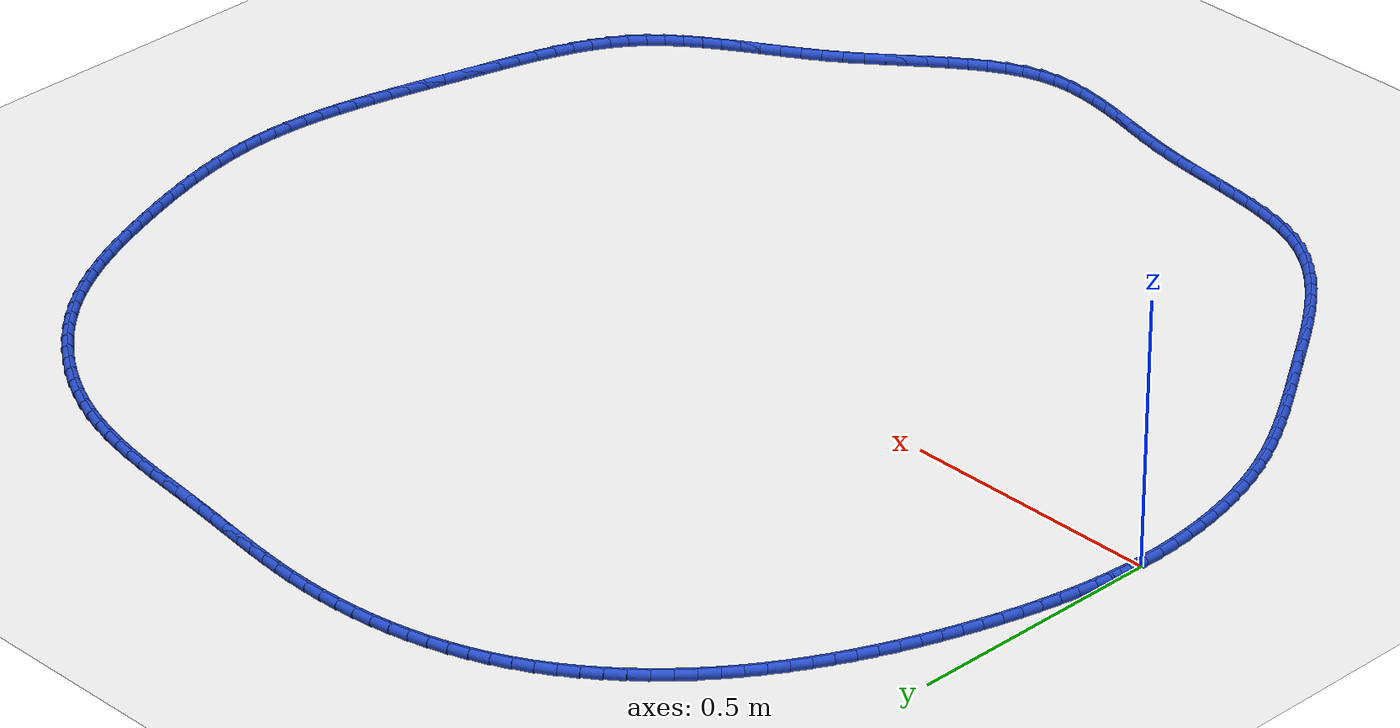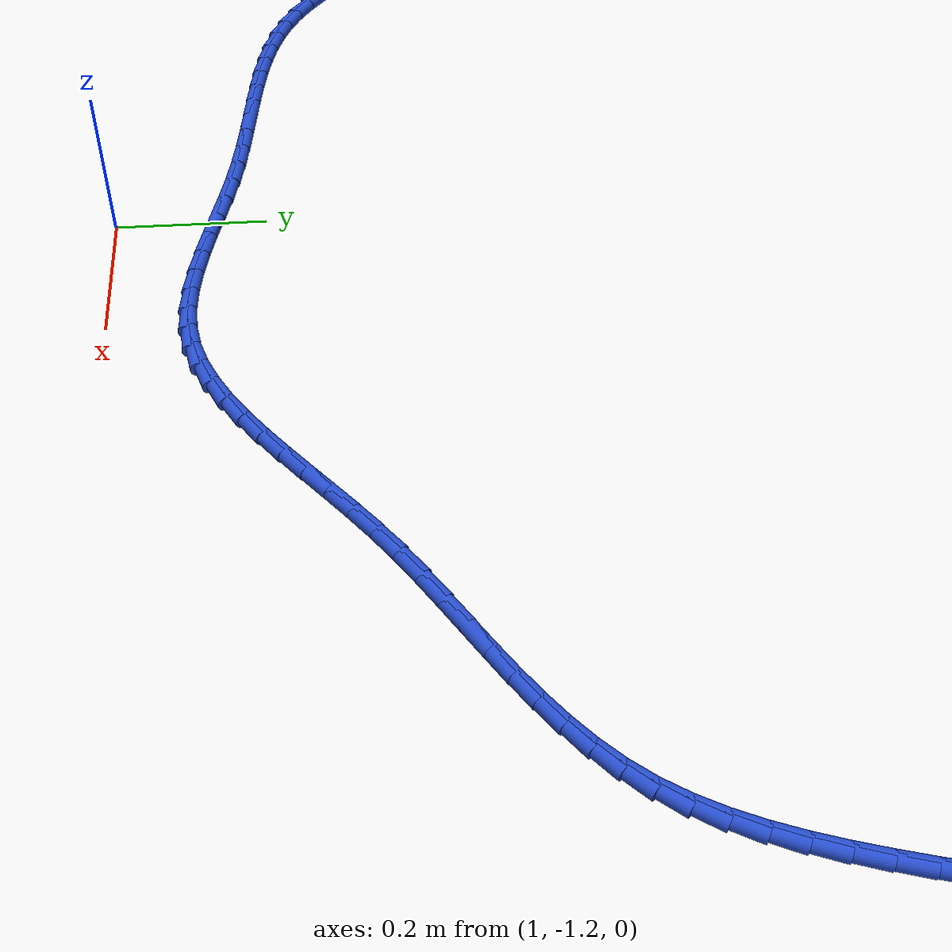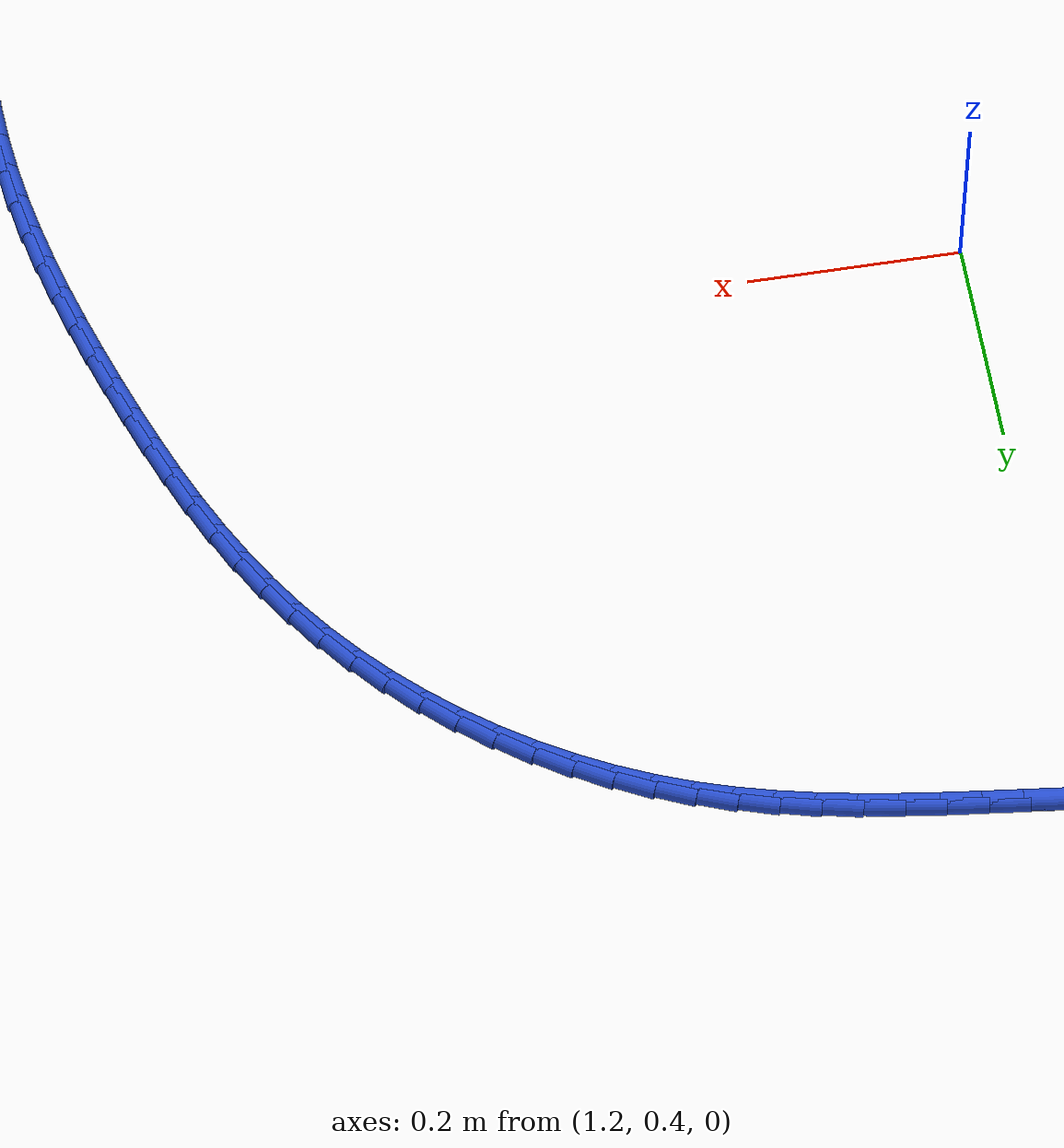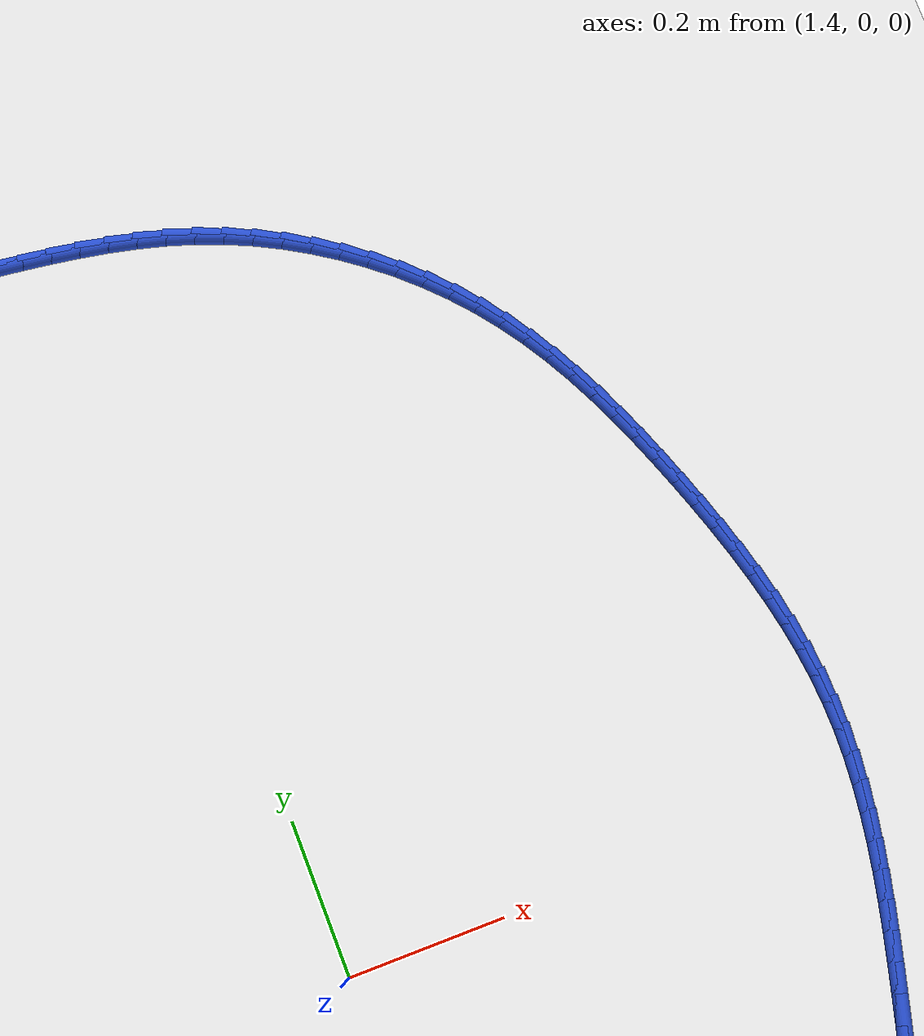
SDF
<sdf version="1.6">
 <world name="default">
  <light name="sun" type="directional">
   <pose>0 0 10 0 -0 0</pose>
   <diffuse>0.8 0.8 0.8 1</diffuse>
   <specular>0.2 0.2 0.2 1</specular>
   <attenuation>
    <range>1000</range>
    <constant>0.9</constant>
    <linear>0.01</linear>
    <quadratic>0.001</quadratic>
   </attenuation>
   <direction>-0.5 0.1 -0.9</direction>
  </light>
  <model name="ground_plane">
   <static>1</static>
   <link name="link">
    <collision name="collision">
     <geometry><plane><normal>0 0 1</normal><size>100 100</size></plane></geometry>
     <surface><friction><ode><mu>100</mu><mu2>50</mu2></ode></friction></surface>
    </collision>
    <visual name="visual">
     <cast_shadows>0</cast_shadows>
     <geometry><plane><normal>0 0 1</normal><size>100 100</size></plane></geometry>
     <material>
      <script><uri>file://media/materials/scripts/gazebo.material</uri><name>Gazebo/WhiteGlow</name></script>
     </material>
    </visual>
   </link>
  </model>
  <gravity>0 0 -9.8</gravity>
  <magnetic_field>6e-06 2.3e-05 -4.2e-05</magnetic_field>
  <atmosphere type="adiabatic"/>
  <physics name="default_physics" default="0" type="ode">
   <max_step_size>0.001</max_step_size>
   <real_time_factor>1</real_time_factor>
   <real_time_update_rate>1000</real_time_update_rate>
  </physics>
  <scene><ambient>0.4 0.4 0.4 1</ambient><background>0.7 0.7 0.7 1</background><shadows>1</shadows></scene>
  <spherical_coordinates>
   <surface_model>EARTH_WGS84</surface_model>
   <latitude_deg>0</latitude_deg>
   <longitude_deg>0</longitude_deg>
   <elevation>0</elevation>
   <heading_deg>0</heading_deg>
  </spherical_coordinates>
  <model name="line">
   <link name="link_0">
    <pose>-1.3877787807814457e-17 -9.71445146547012e-17 0.01 0 1.57 1.53493639392555</pose>
    <collision name="collision">
     <geometry><cylinder><radius>0.01</radius><length>0.08</length></cylinder></geometry>
    </collision>
    <visual name="visual">
     <material>
      <script><name>Gazebo/Blue</name><uri>file://media/materials/scripts/gazebo.material</uri></script>
     </material>
     <geometry><cylinder><radius>0.01</radius><length>0.08</length></cylinder></geometry>
    </visual>
   </link>
   <link name="link_1">
    <pose>0.0013186399837848168 0.03675619560647925 0.01 0 1.57 1.4972960182008648</pose>
    <collision name="collision">
     <geometry><cylinder><radius>0.01</radius><length>0.08</length></cylinder></geometry>
    </collision>
    <visual name="visual">
     <material>
      <script><name>Gazebo/Blue</name><uri>file://media/materials/scripts/gazebo.material</uri></script>
     </material>
     <geometry><cylinder><radius>0.01</radius><length>0.08</length></cylinder></geometry>
    </visual>
   </link>
   <link name="link_2">
    <pose>0.004012989869933039 0.07334782764140409 0.01 0 1.57 1.4615807076959424</pose>
    <collision name="collision">
     <geometry><cylinder><radius>0.01</radius><length>0.08</length></cylinder></geometry>
    </collision>
    <visual name="visual">
     <material>
      <script><name>Gazebo/Blue</name><uri>file://media/materials/scripts/gazebo.material</uri></script>
     </material>
     <geometry><cylinder><radius>0.01</radius><length>0.08</length></cylinder></geometry>
    </visual>
   </link>
   <link name="link_3">
    <pose>0.008007046865664117 0.10977269019210055 0.01 0 1.57 1.4278628527324304</pose>
    <collision name="collision">
     <geometry><cylinder><radius>0.01</radius><length>0.08</length></cylinder></geometry>
    </collision>
    <visual name="visual">
     <material>
      <script><name>Gazebo/Blue</name><uri>file://media/materials/scripts/gazebo.material</uri></script>
     </material>
     <geometry><cylinder><radius>0.01</radius><length>0.08</length></cylinder></geometry>
    </visual>
   </link>
   <link name="link_4">
    <pose>0.013224808178197517 0.1460285773458948 0.01 0 1.57 1.396189340337191</pose>
    <collision name="collision">
     <geometry><cylinder><radius>0.01</radius><length>0.08</length></cylinder></geometry>
    </collision>
    <visual name="visual">
     <material>
      <script><name>Gazebo/Blue</name><uri>file://media/materials/scripts/gazebo.material</uri></script>
     </material>
     <geometry><cylinder><radius>0.01</radius><length>0.08</length></cylinder></geometry>
    </visual>
   </link>
   <link name="link_5">
    <pose>0.0195902710147527 0.18211328319011302 0.01 0 1.57 1.3665851944947651</pose>
    <collision name="collision">
     <geometry><cylinder><radius>0.01</radius><length>0.08</length></cylinder></geometry>
    </collision>
    <visual name="visual">
     <material>
      <script><name>Gazebo/Blue</name><uri>file://media/materials/scripts/gazebo.material</uri></script>
     </material>
     <geometry><cylinder><radius>0.01</radius><length>0.08</length></cylinder></geometry>
    </visual>
   </link>
   <link name="link_6">
    <pose>0.027027432582549117 0.21802460181208128 0.01 0 1.57 1.3390574211833635</pose>
    <collision name="collision">
     <geometry><cylinder><radius>0.01</radius><length>0.08</length></cylinder></geometry>
    </collision>
    <visual name="visual">
     <material>
      <script><name>Gazebo/Blue</name><uri>file://media/materials/scripts/gazebo.material</uri></script>
     </material>
     <geometry><cylinder><radius>0.01</radius><length>0.08</length></cylinder></geometry>
    </visual>
   </link>
   <link name="link_7">
    <pose>0.03546029008880625 0.2537603272991258 0.01 0 1.57 1.3135988222817918</pose>
    <collision name="collision">
     <geometry><cylinder><radius>0.01</radius><length>0.08</length></cylinder></geometry>
    </collision>
    <visual name="visual">
     <material>
      <script><name>Gazebo/Blue</name><uri>file://media/materials/scripts/gazebo.material</uri></script>
     </material>
     <geometry><cylinder><radius>0.01</radius><length>0.08</length></cylinder></geometry>
    </visual>
   </link>
   <link name="link_8">
    <pose>0.04481284074074355 0.2893182537385728 0.01 0 1.57 1.2901916097862556</pose>
    <collision name="collision">
     <geometry><cylinder><radius>0.01</radius><length>0.08</length></cylinder></geometry>
    </collision>
    <visual name="visual">
     <material>
      <script><name>Gazebo/Blue</name><uri>file://media/materials/scripts/gazebo.material</uri></script>
     </material>
     <geometry><cylinder><radius>0.01</radius><length>0.08</length></cylinder></geometry>
    </visual>
   </link>
   <link name="link_9">
    <pose>0.05500908174558049 0.32469617521774835 0.01 0 1.57 1.2687317069449093</pose>
    <collision name="collision">
     <geometry><cylinder><radius>0.01</radius><length>0.08</length></cylinder></geometry>
    </collision>
    <visual name="visual">
     <material>
      <script><name>Gazebo/Blue</name><uri>file://media/materials/scripts/gazebo.material</uri></script>
     </material>
     <geometry><cylinder><radius>0.01</radius><length>0.08</length></cylinder></geometry>
    </visual>
   </link>
   <link name="link_10">
    <pose>0.0659756748409414 0.35989064676023386 0.01 0 1.57 1.2474392900128795</pose>
    <collision name="collision">
     <geometry><cylinder><radius>0.01</radius><length>0.08</length></cylinder></geometry>
    </collision>
    <visual name="visual">
     <material>
      <script><name>Gazebo/Blue</name><uri>file://media/materials/scripts/gazebo.material</uri></script>
     </material>
     <geometry><cylinder><radius>0.01</radius><length>0.08</length></cylinder></geometry>
    </visual>
   </link>
   <link name="link_11">
    <pose>0.07769820583513998 0.39487082243387633 0.01 0 1.57 1.2245590307065426</pose>
    <collision name="collision">
     <geometry><cylinder><radius>0.01</radius><length>0.08</length></cylinder></geometry>
    </collision>
    <visual name="visual">
     <material>
      <script><name>Gazebo/Blue</name><uri>file://media/materials/scripts/gazebo.material</uri></script>
     </material>
     <geometry><cylinder><radius>0.01</radius><length>0.08</length></cylinder></geometry>
    </visual>
   </link>
   <link name="link_12">
    <pose>0.09021990250559205 0.4295790515555042 0.01 0 1.57 1.199969074440465</pose>
    <collision name="collision">
     <geometry><cylinder><radius>0.01</radius><length>0.08</length></cylinder></geometry>
    </collision>
    <visual name="visual">
     <material>
      <script><name>Gazebo/Blue</name><uri>file://media/materials/scripts/gazebo.material</uri></script>
     </material>
     <geometry><cylinder><radius>0.01</radius><length>0.08</length></cylinder></geometry>
    </visual>
   </link>
   <link name="link_13">
    <pose>0.10358640070089928 0.46395656363723464 0.01 0 1.57 1.1736194752285145</pose>
    <collision name="collision">
     <geometry><cylinder><radius>0.01</radius><length>0.08</length></cylinder></geometry>
    </collision>
    <visual name="visual">
     <material>
      <script><name>Gazebo/Blue</name><uri>file://media/materials/scripts/gazebo.material</uri></script>
     </material>
     <geometry><cylinder><radius>0.01</radius><length>0.08</length></cylinder></geometry>
    </visual>
   </link>
   <link name="link_14">
    <pose>0.11784333626966334 0.49794458819118476 0.01 0 1.57 1.145462905295455</pose>
    <collision name="collision">
     <geometry><cylinder><radius>0.01</radius><length>0.08</length></cylinder></geometry>
    </collision>
    <visual name="visual">
     <material>
      <script><name>Gazebo/Blue</name><uri>file://media/materials/scripts/gazebo.material</uri></script>
     </material>
     <geometry><cylinder><radius>0.01</radius><length>0.08</length></cylinder></geometry>
    </visual>
   </link>
   <link name="link_15">
    <pose>0.13303634506048592 0.5314843547294715 0.01 0 1.57 1.1154571440789598</pose>
    <collision name="collision">
     <geometry><cylinder><radius>0.01</radius><length>0.08</length></cylinder></geometry>
    </collision>
    <visual name="visual">
     <material>
      <script><name>Gazebo/Blue</name><uri>file://media/materials/scripts/gazebo.material</uri></script>
     </material>
     <geometry><cylinder><radius>0.01</radius><length>0.08</length></cylinder></geometry>
    </visual>
   </link>
   <link name="link_16">
    <pose>0.14921106292196867 0.5645170927642124 0.01 0 1.57 1.083567963429848</pose>
    <collision name="collision">
     <geometry><cylinder><radius>0.01</radius><length>0.08</length></cylinder></geometry>
    </collision>
    <visual name="visual">
     <material>
      <script><name>Gazebo/Blue</name><uri>file://media/materials/scripts/gazebo.material</uri></script>
     </material>
     <geometry><cylinder><radius>0.01</radius><length>0.08</length></cylinder></geometry>
    </visual>
   </link>
   <link name="link_17">
    <pose>0.16641312570271327 0.5969840318075238 0.01 0 1.57 1.0497724016939556</pose>
    <collision name="collision">
     <geometry><cylinder><radius>0.01</radius><length>0.08</length></cylinder></geometry>
    </collision>
    <visual name="visual">
     <material>
      <script><name>Gazebo/Blue</name><uri>file://media/materials/scripts/gazebo.material</uri></script>
     </material>
     <geometry><cylinder><radius>0.01</radius><length>0.08</length></cylinder></geometry>
    </visual>
   </link>
   <link name="link_18">
    <pose>0.18468816925132148 0.6288264013715232 0.01 0 1.57 1.0140623791485874</pose>
    <collision name="collision">
     <geometry><cylinder><radius>0.01</radius><length>0.08</length></cylinder></geometry>
    </collision>
    <visual name="visual">
     <material>
      <script><name>Gazebo/Blue</name><uri>file://media/materials/scripts/gazebo.material</uri></script>
     </material>
     <geometry><cylinder><radius>0.01</radius><length>0.08</length></cylinder></geometry>
    </visual>
   </link>
   <link name="link_19">
    <pose>0.20408182941639488 0.6599854309683281 0.01 0 1.57 0.9764485542619475</pose>
    <collision name="collision">
     <geometry><cylinder><radius>0.01</radius><length>0.08</length></cylinder></geometry>
    </collision>
    <visual name="visual">
     <material>
      <script><name>Gazebo/Blue</name><uri>file://media/materials/scripts/gazebo.material</uri></script>
     </material>
     <geometry><cylinder><radius>0.01</radius><length>0.08</length></cylinder></geometry>
    </visual>
   </link>
   <link name="link_20">
    <pose>0.22463974204653522 0.690402350110055 0.01 0 1.57 0.936964255825091</pose>
    <collision name="collision">
     <geometry><cylinder><radius>0.01</radius><length>0.08</length></cylinder></geometry>
    </collision>
    <visual name="visual">
     <material>
      <script><name>Gazebo/Blue</name><uri>file://media/materials/scripts/gazebo.material</uri></script>
     </material>
     <geometry><cylinder><radius>0.01</radius><length>0.08</length></cylinder></geometry>
    </visual>
   </link>
   <link name="link_21">
    <pose>0.24640754299034406 0.7200183883088213 0.01 0 1.57 0.8956928046189583</pose>
    <collision name="collision">
     <geometry><cylinder><radius>0.01</radius><length>0.08</length></cylinder></geometry>
    </collision>
    <visual name="visual">
     <material>
      <script><name>Gazebo/Blue</name><uri>file://media/materials/scripts/gazebo.material</uri></script>
     </material>
     <geometry><cylinder><radius>0.01</radius><length>0.08</length></cylinder></geometry>
    </visual>
   </link>
   <link name="link_22">
    <pose>0.2694284776731253 0.7487731773444105 0.01 0 1.57 0.8530732530980307</pose>
    <collision name="collision">
     <geometry><cylinder><radius>0.01</radius><length>0.08</length></cylinder></geometry>
    </collision>
    <visual name="visual">
     <material>
      <script><name>Gazebo/Blue</name><uri>file://media/materials/scripts/gazebo.material</uri></script>
     </material>
     <geometry><cylinder><radius>0.01</radius><length>0.08</length></cylinder></geometry>
    </visual>
   </link>
   <link name="link_23">
    <pose>0.2937034502795244 0.7765780485824891 0.01 0 1.57 0.8092933073116575</pose>
    <collision name="collision">
     <geometry><cylinder><radius>0.01</radius><length>0.08</length></cylinder></geometry>
    </collision>
    <visual name="visual">
     <material>
      <script><name>Gazebo/Blue</name><uri>file://media/materials/scripts/gazebo.material</uri></script>
     </material>
     <geometry><cylinder><radius>0.01</radius><length>0.08</length></cylinder></geometry>
    </visual>
   </link>
   <link name="link_24">
    <pose>0.3191970431813142 0.8033200562931603 0.01 0 1.57 0.7641497401112144</pose>
    <collision name="collision">
     <geometry><cylinder><radius>0.01</radius><length>0.08</length></cylinder></geometry>
    </collision>
    <visual name="visual">
     <material>
      <script><name>Gazebo/Blue</name><uri>file://media/materials/scripts/gazebo.material</uri></script>
     </material>
     <geometry><cylinder><radius>0.01</radius><length>0.08</length></cylinder></geometry>
    </visual>
   </link>
   <link name="link_25">
    <pose>0.345872661093509 0.828885467613853 0.01 0 1.57 0.7174371716382381</pose>
    <collision name="collision">
     <geometry><cylinder><radius>0.01</radius><length>0.08</length></cylinder></geometry>
    </collision>
    <visual name="visual">
     <material>
      <script><name>Gazebo/Blue</name><uri>file://media/materials/scripts/gazebo.material</uri></script>
     </material>
     <geometry><cylinder><radius>0.01</radius><length>0.08</length></cylinder></geometry>
    </visual>
   </link>
   <link name="link_26">
    <pose>0.37369370873112273 0.8531605496819961 0.01 0 1.57 0.668962798000274</pose>
    <collision name="collision">
     <geometry><cylinder><radius>0.01</radius><length>0.08</length></cylinder></geometry>
    </collision>
    <visual name="visual">
     <material>
      <script><name>Gazebo/Blue</name><uri>file://media/materials/scripts/gazebo.material</uri></script>
     </material>
     <geometry><cylinder><radius>0.01</radius><length>0.08</length></cylinder></geometry>
    </visual>
   </link>
   <link name="link_27">
    <pose>0.40262359080916943 0.876031569635019 0.01 0 1.57 0.618551054360377</pose>
    <collision name="collision">
     <geometry><cylinder><radius>0.01</radius><length>0.08</length></cylinder></geometry>
    </collision>
    <visual name="visual">
     <material>
      <script><name>Gazebo/Blue</name><uri>file://media/materials/scripts/gazebo.material</uri></script>
     </material>
     <geometry><cylinder><radius>0.01</radius><length>0.08</length></cylinder></geometry>
    </visual>
   </link>
   <link name="link_28">
    <pose>0.43262571204266376 0.897384794610351 0.01 0 1.57 0.5660499486880994</pose>
    <collision name="collision">
     <geometry><cylinder><radius>0.01</radius><length>0.08</length></cylinder></geometry>
    </collision>
    <visual name="visual">
     <material>
      <script><name>Gazebo/Blue</name><uri>file://media/materials/scripts/gazebo.material</uri></script>
     </material>
     <geometry><cylinder><radius>0.01</radius><length>0.08</length></cylinder></geometry>
    </visual>
   </link>
   <link name="link_29">
    <pose>0.4636634771466193 0.9171064917454208 0.01 0 1.57 0.5113390981478179</pose>
    <collision name="collision">
     <geometry><cylinder><radius>0.01</radius><length>0.08</length></cylinder></geometry>
    </collision>
    <visual name="visual">
     <material>
      <script><name>Gazebo/Blue</name><uri>file://media/materials/scripts/gazebo.material</uri></script>
     </material>
     <geometry><cylinder><radius>0.01</radius><length>0.08</length></cylinder></geometry>
    </visual>
   </link>
   <link name="link_30">
    <pose>0.4957002908360506 0.935082928177658 0.01 0 1.57 0.45474282478008005</pose>
    <collision name="collision">
     <geometry><cylinder><radius>0.01</radius><length>0.08</length></cylinder></geometry>
    </collision>
    <visual name="visual">
     <material>
      <script><name>Gazebo/Blue</name><uri>file://media/materials/scripts/gazebo.material</uri></script>
     </material>
     <geometry><cylinder><radius>0.01</radius><length>0.08</length></cylinder></geometry>
    </visual>
   </link>
   <link name="link_31">
    <pose>0.528693932313233 0.9512141156221596 0.01 0 1.57 0.3993133383227738</pose>
    <collision name="collision">
     <geometry><cylinder><radius>0.01</radius><length>0.08</length></cylinder></geometry>
    </collision>
    <visual name="visual">
     <material>
      <script><name>Gazebo/Blue</name><uri>file://media/materials/scripts/gazebo.material</uri></script>
     </material>
     <geometry><cylinder><radius>0.01</radius><length>0.08</length></cylinder></geometry>
    </visual>
   </link>
   <link name="link_32">
    <pose>0.5625593258335817 0.9655047714756152 0.01 0 1.57 0.34645957079151485</pose>
    <collision name="collision">
     <geometry><cylinder><radius>0.01</radius><length>0.08</length></cylinder></geometry>
    </collision>
    <visual name="visual">
     <material>
      <script><name>Gazebo/Blue</name><uri>file://media/materials/scripts/gazebo.material</uri></script>
     </material>
     <geometry><cylinder><radius>0.01</radius><length>0.08</length></cylinder></geometry>
    </visual>
   </link>
   <link name="link_33">
    <pose>0.5971916758354735 0.9780077937307731 0.01 0 1.57 0.2961347690362358</pose>
    <collision name="collision">
     <geometry><cylinder><radius>0.01</radius><length>0.08</length></cylinder></geometry>
    </collision>
    <visual name="visual">
     <material>
      <script><name>Gazebo/Blue</name><uri>file://media/materials/scripts/gazebo.material</uri></script>
     </material>
     <geometry><cylinder><radius>0.01</radius><length>0.08</length></cylinder></geometry>
    </visual>
   </link>
   <link name="link_34">
    <pose>0.6324860822223001 0.9887763357862958 0.01 0 1.57 0.2482397640339947</pose>
    <collision name="collision">
     <geometry><cylinder><radius>0.01</radius><length>0.08</length></cylinder></geometry>
    </collision>
    <visual name="visual">
     <material>
      <script><name>Gazebo/Blue</name><uri>file://media/materials/scripts/gazebo.material</uri></script>
     </material>
     <geometry><cylinder><radius>0.01</radius><length>0.08</length></cylinder></geometry>
    </visual>
   </link>
   <link name="link_35">
    <pose>0.6683376448974537 0.9978635510408455 0.01 0 1.57 0.20264157041888395</pose>
    <collision name="collision">
     <geometry><cylinder><radius>0.01</radius><length>0.08</length></cylinder></geometry>
    </collision>
    <visual name="visual">
     <material>
      <script><name>Gazebo/Blue</name><uri>file://media/materials/scripts/gazebo.material</uri></script>
     </material>
     <geometry><cylinder><radius>0.01</radius><length>0.08</length></cylinder></geometry>
    </visual>
   </link>
   <link name="link_36">
    <pose>0.704641463764326 1.0053225928930847 0.01 0 1.57 0.1591828618495089</pose>
    <collision name="collision">
     <geometry><cylinder><radius>0.01</radius><length>0.08</length></cylinder></geometry>
    </collision>
    <visual name="visual">
     <material>
      <script><name>Gazebo/Blue</name><uri>file://media/materials/scripts/gazebo.material</uri></script>
     </material>
     <geometry><cylinder><radius>0.01</radius><length>0.08</length></cylinder></geometry>
    </visual>
   </link>
   <link name="link_37">
    <pose>0.7412926387263085 1.0112066147416758 0.01 0 1.57 0.11768960297802805</pose>
    <collision name="collision">
     <geometry><cylinder><radius>0.01</radius><length>0.08</length></cylinder></geometry>
    </collision>
    <visual name="visual">
     <material>
      <script><name>Gazebo/Blue</name><uri>file://media/materials/scripts/gazebo.material</uri></script>
     </material>
     <geometry><cylinder><radius>0.01</radius><length>0.08</length></cylinder></geometry>
    </visual>
   </link>
   <link name="link_38">
    <pose>0.7781862696867932 1.0155687699852811 0.01 0 1.57 0.07797684832110709</pose>
    <collision name="collision">
     <geometry><cylinder><radius>0.01</radius><length>0.08</length></cylinder></geometry>
    </collision>
    <visual name="visual">
     <material>
      <script><name>Gazebo/Blue</name><uri>file://media/materials/scripts/gazebo.material</uri></script>
     </material>
     <geometry><cylinder><radius>0.01</radius><length>0.08</length></cylinder></geometry>
    </visual>
   </link>
   <link name="link_39">
    <pose>0.8152174565491722 1.0184622120225633 0.01 0 1.57 0.039852849169684706</pose>
    <collision name="collision">
     <geometry><cylinder><radius>0.01</radius><length>0.08</length></cylinder></geometry>
    </collision>
    <visual name="visual">
     <material>
      <script><name>Gazebo/Blue</name><uri>file://media/materials/scripts/gazebo.material</uri></script>
     </material>
     <geometry><cylinder><radius>0.01</radius><length>0.08</length></cylinder></geometry>
    </visual>
   </link>
   <link name="link_40">
    <pose>0.8522812992168369 1.0199400942521841 0.01 0 1.57 0.00312166682691249</pose>
    <collision name="collision">
     <geometry><cylinder><radius>0.01</radius><length>0.08</length></cylinder></geometry>
    </collision>
    <visual name="visual">
     <material>
      <script><name>Gazebo/Blue</name><uri>file://media/materials/scripts/gazebo.material</uri></script>
     </material>
     <geometry><cylinder><radius>0.01</radius><length>0.08</length></cylinder></geometry>
    </visual>
   </link>
   <link name="link_41">
    <pose>0.8892728975931793 1.0200555700728067 0.01 0 1.57 -0.03236474012850684</pose>
    <collision name="collision">
     <geometry><cylinder><radius>0.01</radius><length>0.08</length></cylinder></geometry>
    </collision>
    <visual name="visual">
     <material>
      <script><name>Gazebo/Blue</name><uri>file://media/materials/scripts/gazebo.material</uri></script>
     </material>
     <geometry><cylinder><radius>0.01</radius><length>0.08</length></cylinder></geometry>
    </visual>
   </link>
   <link name="link_42">
    <pose>0.9260890296478109 1.0188636093136663 0.01 0 1.57 -0.06479041760330709</pose>
    <collision name="collision">
     <geometry><cylinder><radius>0.01</radius><length>0.08</length></cylinder></geometry>
    </collision>
    <visual name="visual">
     <material>
      <script><name>Gazebo/Blue</name><uri>file://media/materials/scripts/gazebo.material</uri></script>
     </material>
     <geometry><cylinder><radius>0.01</radius><length>0.08</length></cylinder></geometry>
    </visual>
   </link>
   <link name="link_43">
    <pose>0.9626908252589149 1.0164888398263159 0.01 0 1.57 -0.09150485835991794</pose>
    <collision name="collision">
     <geometry><cylinder><radius>0.01</radius><length>0.08</length></cylinder></geometry>
    </collision>
    <visual name="visual">
     <material>
      <script><name>Gazebo/Blue</name><uri>file://media/materials/scripts/gazebo.material</uri></script>
     </material>
     <geometry><cylinder><radius>0.01</radius><length>0.08</length></cylinder></geometry>
    </visual>
   </link>
   <link name="link_44">
    <pose>0.9991225024860165 1.0131458286501067 0.01 0 1.57 -0.11218427442498657</pose>
    <collision name="collision">
     <geometry><cylinder><radius>0.01</radius><length>0.08</length></cylinder></geometry>
    </collision>
    <visual name="visual">
     <material>
      <script><name>Gazebo/Blue</name><uri>file://media/materials/scripts/gazebo.material</uri></script>
     </material>
     <geometry><cylinder><radius>0.01</radius><length>0.08</length></cylinder></geometry>
    </visual>
   </link>
   <link name="link_45">
    <pose>1.0354337815816534 1.0090550986987714 0.01 0 1.57 -0.1267410793708616</pose>
    <collision name="collision">
     <geometry><cylinder><radius>0.01</radius><length>0.08</length></cylinder></geometry>
    </collision>
    <visual name="visual">
     <material>
      <script><name>Gazebo/Blue</name><uri>file://media/materials/scripts/gazebo.material</uri></script>
     </material>
     <geometry><cylinder><radius>0.01</radius><length>0.08</length></cylinder></geometry>
    </visual>
   </link>
   <link name="link_46">
    <pose>1.071674382798363 1.0044371728860426 0.01 0 1.57 -0.13513619637270025</pose>
    <collision name="collision">
     <geometry><cylinder><radius>0.01</radius><length>0.08</length></cylinder></geometry>
    </collision>
    <visual name="visual">
     <material>
      <script><name>Gazebo/Blue</name><uri>file://media/materials/scripts/gazebo.material</uri></script>
     </material>
     <geometry><cylinder><radius>0.01</radius><length>0.08</length></cylinder></geometry>
    </visual>
   </link>
   <link name="link_47">
    <pose>1.1078940263886827 0.9995125741256525 0.01 0 1.57 -0.1373631088422806</pose>
    <collision name="collision">
     <geometry><cylinder><radius>0.01</radius><length>0.08</length></cylinder></geometry>
    </collision>
    <visual name="visual">
     <material>
      <script><name>Gazebo/Blue</name><uri>file://media/materials/scripts/gazebo.material</uri></script>
     </material>
     <geometry><cylinder><radius>0.01</radius><length>0.08</length></cylinder></geometry>
    </visual>
   </link>
   <link name="link_48">
    <pose>1.14414243260515 0.9945018253313338 0.01 0 1.57 -0.13343831675446832</pose>
    <collision name="collision">
     <geometry><cylinder><radius>0.01</radius><length>0.08</length></cylinder></geometry>
    </collision>
    <visual name="visual">
     <material>
      <script><name>Gazebo/Blue</name><uri>file://media/materials/scripts/gazebo.material</uri></script>
     </material>
     <geometry><cylinder><radius>0.01</radius><length>0.08</length></cylinder></geometry>
    </visual>
   </link>
   <link name="link_49">
    <pose>1.1804693217003033 0.9896254494168188 0.01 0 1.57 -0.1241115976965939</pose>
    <collision name="collision">
     <geometry><cylinder><radius>0.01</radius><length>0.08</length></cylinder></geometry>
    </collision>
    <visual name="visual">
     <material>
      <script><name>Gazebo/Blue</name><uri>file://media/materials/scripts/gazebo.material</uri></script>
     </material>
     <geometry><cylinder><radius>0.01</radius><length>0.08</length></cylinder></geometry>
    </visual>
   </link>
   <link name="link_50">
    <pose>1.2169179076732959 0.9850783859840062 0.01 0 1.57 -0.11703241086616221</pose>
    <collision name="collision">
     <geometry><cylinder><radius>0.01</radius><length>0.08</length></cylinder></geometry>
    </collision>
    <visual name="visual">
     <material>
      <script><name>Gazebo/Blue</name><uri>file://media/materials/scripts/gazebo.material</uri></script>
     </material>
     <geometry><cylinder><radius>0.01</radius><length>0.08</length></cylinder></geometry>
    </visual>
   </link>
   <link name="link_51">
    <pose>1.2534618125292718 0.9807819311753098 0.01 0 1.57 -0.11678503627030312</pose>
    <collision name="collision">
     <geometry><cylinder><radius>0.01</radius><length>0.08</length></cylinder></geometry>
    </collision>
    <visual name="visual">
     <material>
      <script><name>Gazebo/Blue</name><uri>file://media/materials/scripts/gazebo.material</uri></script>
     </material>
     <geometry><cylinder><radius>0.01</radius><length>0.08</length></cylinder></geometry>
    </visual>
   </link>
   <link name="link_52">
    <pose>1.2900324725567665 0.9764915022041387 0.01 0 1.57 -0.12341890405643915</pose>
    <collision name="collision">
     <geometry><cylinder><radius>0.01</radius><length>0.08</length></cylinder></geometry>
    </collision>
    <visual name="visual">
     <material>
      <script><name>Gazebo/Blue</name><uri>file://media/materials/scripts/gazebo.material</uri></script>
     </material>
     <geometry><cylinder><radius>0.01</radius><length>0.08</length></cylinder></geometry>
    </visual>
   </link>
   <link name="link_53">
    <pose>1.3265607333447897 0.971960193587693 0.01 0 1.57 -0.13696106924578758</pose>
    <collision name="collision">
     <geometry><cylinder><radius>0.01</radius><length>0.08</length></cylinder></geometry>
    </collision>
    <visual name="visual">
     <material>
      <script><name>Gazebo/Blue</name><uri>file://media/materials/scripts/gazebo.material</uri></script>
     </material>
     <geometry><cylinder><radius>0.01</radius><length>0.08</length></cylinder></geometry>
    </visual>
   </link>
   <link name="link_54">
    <pose>1.3629774404823563 0.9669410998431742 0.01 0 1.57 -0.15747174510346842</pose>
    <collision name="collision">
     <geometry><cylinder><radius>0.01</radius><length>0.08</length></cylinder></geometry>
    </collision>
    <visual name="visual">
     <material>
      <script><name>Gazebo/Blue</name><uri>file://media/materials/scripts/gazebo.material</uri></script>
     </material>
     <geometry><cylinder><radius>0.01</radius><length>0.08</length></cylinder></geometry>
    </visual>
   </link>
   <link name="link_55">
    <pose>1.3992134395584779 0.961187315487783 0.01 0 1.57 -0.1850252525510422</pose>
    <collision name="collision">
     <geometry><cylinder><radius>0.01</radius><length>0.08</length></cylinder></geometry>
    </collision>
    <visual name="visual">
     <material>
      <script><name>Gazebo/Blue</name><uri>file://media/materials/scripts/gazebo.material</uri></script>
     </material>
     <geometry><cylinder><radius>0.01</radius><length>0.08</length></cylinder></geometry>
    </visual>
   </link>
   <link name="link_56">
    <pose>1.435199576162166 0.9544519350387198 0.01 0 1.57 -0.21968012567694756</pose>
    <collision name="collision">
     <geometry><cylinder><radius>0.01</radius><length>0.08</length></cylinder></geometry>
    </collision>
    <visual name="visual">
     <material>
      <script><name>Gazebo/Blue</name><uri>file://media/materials/scripts/gazebo.material</uri></script>
     </material>
     <geometry><cylinder><radius>0.01</radius><length>0.08</length></cylinder></geometry>
    </visual>
   </link>
   <link name="link_57">
    <pose>1.4708666958824341 0.9464880530131861 0.01 0 1.57 -0.26143764998200736</pose>
    <collision name="collision">
     <geometry><cylinder><radius>0.01</radius><length>0.08</length></cylinder></geometry>
    </collision>
    <visual name="visual">
     <material>
      <script><name>Gazebo/Blue</name><uri>file://media/materials/scripts/gazebo.material</uri></script>
     </material>
     <geometry><cylinder><radius>0.01</radius><length>0.08</length></cylinder></geometry>
    </visual>
   </link>
   <link name="link_58">
    <pose>1.5061456443082946 0.937048763928382 0.01 0 1.57 -0.3101895486557157</pose>
    <collision name="collision">
     <geometry><cylinder><radius>0.01</radius><length>0.08</length></cylinder></geometry>
    </collision>
    <visual name="visual">
     <material>
      <script><name>Gazebo/Blue</name><uri>file://media/materials/scripts/gazebo.material</uri></script>
     </material>
     <geometry><cylinder><radius>0.01</radius><length>0.08</length></cylinder></geometry>
    </visual>
   </link>
   <link name="link_59">
    <pose>1.5409672670287589 0.9258871623015088 0.01 0 1.57 -0.3653326151483972</pose>
    <collision name="collision">
     <geometry><cylinder><radius>0.01</radius><length>0.08</length></cylinder></geometry>
    </collision>
    <visual name="visual">
     <material>
      <script><name>Gazebo/Blue</name><uri>file://media/materials/scripts/gazebo.material</uri></script>
     </material>
     <geometry><cylinder><radius>0.01</radius><length>0.08</length></cylinder></geometry>
    </visual>
   </link>
   <link name="link_60">
    <pose>1.5752601894281915 0.9127700066724777 0.01 0 1.57 -0.42214149033342035</pose>
    <collision name="collision">
     <geometry><cylinder><radius>0.01</radius><length>0.08</length></cylinder></geometry>
    </collision>
    <visual name="visual">
     <material>
      <script><name>Gazebo/Blue</name><uri>file://media/materials/scripts/gazebo.material</uri></script>
     </material>
     <geometry><cylinder><radius>0.01</radius><length>0.08</length></cylinder></geometry>
    </visual>
   </link>
   <link name="link_61">
    <pose>1.6089227095334984 0.8976507022045873 0.01 0 1.57 -0.4776172571557755</pose>
    <collision name="collision">
     <geometry><cylinder><radius>0.01</radius><length>0.08</length></cylinder></geometry>
    </collision>
    <visual name="visual">
     <material>
      <script><name>Gazebo/Blue</name><uri>file://media/materials/scripts/gazebo.material</uri></script>
     </material>
     <geometry><cylinder><radius>0.01</radius><length>0.08</length></cylinder></geometry>
    </visual>
   </link>
   <link name="link_62">
    <pose>1.6418311759731725 0.880617739391444 0.01 0 1.57 -0.5320436662417818</pose>
    <collision name="collision">
     <geometry><cylinder><radius>0.01</radius><length>0.08</length></cylinder></geometry>
    </collision>
    <visual name="visual">
     <material>
      <script><name>Gazebo/Blue</name><uri>file://media/materials/scripts/gazebo.material</uri></script>
     </material>
     <geometry><cylinder><radius>0.01</radius><length>0.08</length></cylinder></geometry>
    </visual>
   </link>
   <link name="link_63">
    <pose>1.6738614478613179 0.8617626213929599 0.01 0 1.57 -0.5857787641336437</pose>
    <collision name="collision">
     <geometry><cylinder><radius>0.01</radius><length>0.08</length></cylinder></geometry>
    </collision>
    <visual name="visual">
     <material>
      <script><name>Gazebo/Blue</name><uri>file://media/materials/scripts/gazebo.material</uri></script>
     </material>
     <geometry><cylinder><radius>0.01</radius><length>0.08</length></cylinder></geometry>
    </visual>
   </link>
   <link name="link_64">
    <pose>1.7048893843120374 0.8411768513690479 0.01 0 1.57 -0.6391812825142309</pose>
    <collision name="collision">
     <geometry><cylinder><radius>0.01</radius><length>0.08</length></cylinder></geometry>
    </collision>
    <visual name="visual">
     <material>
      <script><name>Gazebo/Blue</name><uri>file://media/materials/scripts/gazebo.material</uri></script>
     </material>
     <geometry><cylinder><radius>0.01</radius><length>0.08</length></cylinder></geometry>
    </visual>
   </link>
   <link name="link_65">
    <pose>1.7347908444394344 0.8189519324796196 0.01 0 1.57 -0.6926100284502452</pose>
    <collision name="collision">
     <geometry><cylinder><radius>0.01</radius><length>0.08</length></cylinder></geometry>
    </collision>
    <visual name="visual">
     <material>
      <script><name>Gazebo/Blue</name><uri>file://media/materials/scripts/gazebo.material</uri></script>
     </material>
     <geometry><cylinder><radius>0.01</radius><length>0.08</length></cylinder></geometry>
    </visual>
   </link>
   <link name="link_66">
    <pose>1.7634416873576124 0.7951793678845873 0.01 0 1.57 -0.7464237984970812</pose>
    <collision name="collision">
     <geometry><cylinder><radius>0.01</radius><length>0.08</length></cylinder></geometry>
    </collision>
    <visual name="visual">
     <material>
      <script><name>Gazebo/Blue</name><uri>file://media/materials/scripts/gazebo.material</uri></script>
     </material>
     <geometry><cylinder><radius>0.01</radius><length>0.08</length></cylinder></geometry>
    </visual>
   </link>
   <link name="link_67">
    <pose>1.7907177721806746 0.769950660743864 0.01 0 1.57 -0.8009812515004475</pose>
    <collision name="collision">
     <geometry><cylinder><radius>0.01</radius><length>0.08</length></cylinder></geometry>
    </collision>
    <visual name="visual">
     <material>
      <script><name>Gazebo/Blue</name><uri>file://media/materials/scripts/gazebo.material</uri></script>
     </material>
     <geometry><cylinder><radius>0.01</radius><length>0.08</length></cylinder></geometry>
    </visual>
   </link>
   <link name="link_68">
    <pose>1.8164949580227243 0.7433573142173615 0.01 0 1.57 -0.8566401722104824</pose>
    <collision name="collision">
     <geometry><cylinder><radius>0.01</radius><length>0.08</length></cylinder></geometry>
    </collision>
    <visual name="visual">
     <material>
      <script><name>Gazebo/Blue</name><uri>file://media/materials/scripts/gazebo.material</uri></script>
     </material>
     <geometry><cylinder><radius>0.01</radius><length>0.08</length></cylinder></geometry>
    </visual>
   </link>
   <link name="link_69">
    <pose>1.8406491039978654 0.7154908314649919 0.01 0 1.57 -0.913693137524716</pose>
    <collision name="collision">
     <geometry><cylinder><radius>0.01</radius><length>0.08</length></cylinder></geometry>
    </collision>
    <visual name="visual">
     <material>
      <script><name>Gazebo/Blue</name><uri>file://media/materials/scripts/gazebo.material</uri></script>
     </material>
     <geometry><cylinder><radius>0.01</radius><length>0.08</length></cylinder></geometry>
    </visual>
   </link>
   <link name="link_70">
    <pose>1.8630588717643106 0.686442829546759 0.01 0 1.57 -0.9697912031403088</pose>
    <collision name="collision">
     <geometry><cylinder><radius>0.01</radius><length>0.08</length></cylinder></geometry>
    </collision>
    <visual name="visual">
     <material>
      <script><name>Gazebo/Blue</name><uri>file://media/materials/scripts/gazebo.material</uri></script>
     </material>
     <geometry><cylinder><radius>0.01</radius><length>0.08</length></cylinder></geometry>
    </visual>
   </link>
   <link name="link_71">
    <pose>1.883718599030442 0.65630962679127 0.01 0 1.57 -1.021239423830846</pose>
    <collision name="collision">
     <geometry><cylinder><radius>0.01</radius><length>0.08</length></cylinder></geometry>
    </collision>
    <visual name="visual">
     <material>
      <script><name>Gazebo/Blue</name><uri>file://media/materials/scripts/gazebo.material</uri></script>
     </material>
     <geometry><cylinder><radius>0.01</radius><length>0.08</length></cylinder></geometry>
    </visual>
   </link>
   <link name="link_72">
    <pose>1.9027769026811145 0.6251938116915063 0.01 0 1.57 -1.0675033149352238</pose>
    <collision name="collision">
     <geometry><cylinder><radius>0.01</radius><length>0.08</length></cylinder></geometry>
    </collision>
    <visual name="visual">
     <material>
      <script><name>Gazebo/Blue</name><uri>file://media/materials/scripts/gazebo.material</uri></script>
     </material>
     <geometry><cylinder><radius>0.01</radius><length>0.08</length></cylinder></geometry>
    </visual>
   </link>
   <link name="link_73">
    <pose>1.9203931240312633 0.5931984085992671 0.01 0 1.57 -1.108431195358011</pose>
    <collision name="collision">
     <geometry><cylinder><radius>0.01</radius><length>0.08</length></cylinder></geometry>
    </collision>
    <visual name="visual">
     <material>
      <script><name>Gazebo/Blue</name><uri>file://media/materials/scripts/gazebo.material</uri></script>
     </material>
     <geometry><cylinder><radius>0.01</radius><length>0.08</length></cylinder></geometry>
    </visual>
   </link>
   <link name="link_74">
    <pose>1.9367266043958222 0.5604264418663504 0.01 0 1.57 -1.143981070764763</pose>
    <collision name="collision">
     <geometry><cylinder><radius>0.01</radius><length>0.08</length></cylinder></geometry>
    </collision>
    <visual name="visual">
     <material>
      <script><name>Gazebo/Blue</name><uri>file://media/materials/scripts/gazebo.material</uri></script>
     </material>
     <geometry><cylinder><radius>0.01</radius><length>0.08</length></cylinder></geometry>
    </visual>
   </link>
   <link name="link_75">
    <pose>1.9519366850897248 0.5269809358445559 0.01 0 1.57 -1.174186013063726</pose>
    <collision name="collision">
     <geometry><cylinder><radius>0.01</radius><length>0.08</length></cylinder></geometry>
    </collision>
    <visual name="visual">
     <material>
      <script><name>Gazebo/Blue</name><uri>file://media/materials/scripts/gazebo.material</uri></script>
     </material>
     <geometry><cylinder><radius>0.01</radius><length>0.08</length></cylinder></geometry>
    </visual>
   </link>
   <link name="link_76">
    <pose>1.9661827074279046 0.49296491488568145 0.01 0 1.57 -1.1991231123865576</pose>
    <collision name="collision">
     <geometry><cylinder><radius>0.01</radius><length>0.08</length></cylinder></geometry>
    </collision>
    <visual name="visual">
     <material>
      <script><name>Gazebo/Blue</name><uri>file://media/materials/scripts/gazebo.material</uri></script>
     </material>
     <geometry><cylinder><radius>0.01</radius><length>0.08</length></cylinder></geometry>
    </visual>
   </link>
   <link name="link_77">
    <pose>1.9796240127252962 0.458481403341526 0.01 0 1.57 -1.2188877542748837</pose>
    <collision name="collision">
     <geometry><cylinder><radius>0.01</radius><length>0.08</length></cylinder></geometry>
    </collision>
    <visual name="visual">
     <material>
      <script><name>Gazebo/Blue</name><uri>file://media/materials/scripts/gazebo.material</uri></script>
     </material>
     <geometry><cylinder><radius>0.01</radius><length>0.08</length></cylinder></geometry>
    </visual>
   </link>
   <link name="link_78">
    <pose>1.9924199422968323 0.42363342556388867 0.01 0 1.57 -1.2349421339759947</pose>
    <collision name="collision">
     <geometry><cylinder><radius>0.01</radius><length>0.08</length></cylinder></geometry>
    </collision>
    <visual name="visual">
     <material>
      <script><name>Gazebo/Blue</name><uri>file://media/materials/scripts/gazebo.material</uri></script>
     </material>
     <geometry><cylinder><radius>0.01</radius><length>0.08</length></cylinder></geometry>
    </visual>
   </link>
   <link name="link_79">
    <pose>2.004679489474283 0.3885137441155916 0.01 0 1.57 -1.2532630219608907</pose>
    <collision name="collision">
     <geometry><cylinder><radius>0.01</radius><length>0.08</length></cylinder></geometry>
    </collision>
    <visual name="visual">
     <material>
      <script><name>Gazebo/Blue</name><uri>file://media/materials/scripts/gazebo.material</uri></script>
     </material>
     <geometry><cylinder><radius>0.01</radius><length>0.08</length></cylinder></geometry>
    </visual>
   </link>
   <link name="link_80">
    <pose>2.016295034657953 0.35317097210097603 0.01 0 1.57 -1.2755494375261012</pose>
    <collision name="collision">
     <geometry><cylinder><radius>0.01</radius><length>0.08</length></cylinder></geometry>
    </collision>
    <visual name="visual">
     <material>
      <script><name>Gazebo/Blue</name><uri>file://media/materials/scripts/gazebo.material</uri></script>
     </material>
     <geometry><cylinder><radius>0.01</radius><length>0.08</length></cylinder></geometry>
    </visual>
   </link>
   <link name="link_81">
    <pose>2.0271007165072614 0.3176418519511814 0.01 0 1.57 -1.3019531537388538</pose>
    <collision name="collision">
     <geometry><cylinder><radius>0.01</radius><length>0.08</length></cylinder></geometry>
    </collision>
    <visual name="visual">
     <material>
      <script><name>Gazebo/Blue</name><uri>file://media/materials/scripts/gazebo.material</uri></script>
     </material>
     <geometry><cylinder><radius>0.01</radius><length>0.08</length></cylinder></geometry>
    </visual>
   </link>
   <link name="link_82">
    <pose>2.0369306729060135 0.2819631259392626 0.01 0 1.57 -1.3326537900142688</pose>
    <collision name="collision">
     <geometry><cylinder><radius>0.01</radius><length>0.08</length></cylinder></geometry>
    </collision>
    <visual name="visual">
     <material>
      <script><name>Gazebo/Blue</name><uri>file://media/materials/scripts/gazebo.material</uri></script>
     </material>
     <geometry><cylinder><radius>0.01</radius><length>0.08</length></cylinder></geometry>
    </visual>
   </link>
   <link name="link_83">
    <pose>2.0456190417380165 0.2461715363382743 0.01 0 1.57 -1.3678476548385323</pose>
    <collision name="collision">
     <geometry><cylinder><radius>0.01</radius><length>0.08</length></cylinder></geometry>
    </collision>
    <visual name="visual">
     <material>
      <script><name>Gazebo/Blue</name><uri>file://media/materials/scripts/gazebo.material</uri></script>
     </material>
     <geometry><cylinder><radius>0.01</radius><length>0.08</length></cylinder></geometry>
    </visual>
   </link>
   <link name="link_84">
    <pose>2.0529999608870746 0.21030382542127224 0.01 0 1.57 -1.4077323337502987</pose>
    <collision name="collision">
     <geometry><cylinder><radius>0.01</radius><length>0.08</length></cylinder></geometry>
    </collision>
    <visual name="visual">
     <material>
      <script><name>Gazebo/Blue</name><uri>file://media/materials/scripts/gazebo.material</uri></script>
     </material>
     <geometry><cylinder><radius>0.01</radius><length>0.08</length></cylinder></geometry>
    </visual>
   </link>
   <link name="link_85">
    <pose>2.058907568236993 0.17439673546131088 0.01 0 1.57 -1.4524857859428293</pose>
    <collision name="collision">
     <geometry><cylinder><radius>0.01</radius><length>0.08</length></cylinder></geometry>
    </collision>
    <visual name="visual">
     <material>
      <script><name>Gazebo/Blue</name><uri>file://media/materials/scripts/gazebo.material</uri></script>
     </material>
     <geometry><cylinder><radius>0.01</radius><length>0.08</length></cylinder></geometry>
    </visual>
   </link>
   <link name="link_86">
    <pose>2.063176001671578 0.13848700873144587 0.01 0 1.57 -1.502238902006572</pose>
    <collision name="collision">
     <geometry><cylinder><radius>0.01</radius><length>0.08</length></cylinder></geometry>
    </collision>
    <visual name="visual">
     <material>
      <script><name>Gazebo/Blue</name><uri>file://media/materials/scripts/gazebo.material</uri></script>
     </material>
     <geometry><cylinder><radius>0.01</radius><length>0.08</length></cylinder></geometry>
    </visual>
   </link>
   <link name="link_87">
    <pose>2.065639402556073 0.10261138686794108 0.01 0 1.57 -1.5552907972759409</pose>
    <collision name="collision">
     <geometry><cylinder><radius>0.01</radius><length>0.08</length></cylinder></geometry>
    </collision>
    <visual name="visual">
     <material>
      <script><name>Gazebo/Blue</name><uri>file://media/materials/scripts/gazebo.material</uri></script>
     </material>
     <geometry><cylinder><radius>0.01</radius><length>0.08</length></cylinder></geometry>
    </visual>
   </link>
   <link name="link_88">
    <pose>2.0661947974176416 0.06679510916104645 0.01 0 1.57 1.536364882962839</pose>
    <collision name="collision">
     <geometry><cylinder><radius>0.01</radius><length>0.08</length></cylinder></geometry>
    </collision>
    <visual name="visual">
     <material>
      <script><name>Gazebo/Blue</name><uri>file://media/materials/scripts/gazebo.material</uri></script>
     </material>
     <geometry><cylinder><radius>0.01</radius><length>0.08</length></cylinder></geometry>
    </visual>
   </link>
   <link name="link_89">
    <pose>2.064962609701651 0.0310225532959361 0.01 0 1.57 1.4912587195037728</pose>
    <collision name="collision">
     <geometry><cylinder><radius>0.01</radius><length>0.08</length></cylinder></geometry>
    </collision>
    <visual name="visual">
     <material>
      <script><name>Gazebo/Blue</name><uri>file://media/materials/scripts/gazebo.material</uri></script>
     </material>
     <geometry><cylinder><radius>0.01</radius><length>0.08</length></cylinder></geometry>
    </visual>
   </link>
   <link name="link_90">
    <pose>2.062112847842518 -0.004730972649159733 0.01 0 1.57 1.4511957939687348</pose>
    <collision name="collision">
     <geometry><cylinder><radius>0.01</radius><length>0.08</length></cylinder></geometry>
    </collision>
    <visual name="visual">
     <material>
      <script><name>Gazebo/Blue</name><uri>file://media/materials/scripts/gazebo.material</uri></script>
     </material>
     <geometry><cylinder><radius>0.01</radius><length>0.08</length></cylinder></geometry>
    </visual>
   </link>
   <link name="link_91">
    <pose>2.057815520274661 -0.04049016059601057 0.01 0 1.57 1.416269600788045</pose>
    <collision name="collision">
     <geometry><cylinder><radius>0.01</radius><length>0.08</length></cylinder></geometry>
    </collision>
    <visual name="visual">
     <material>
      <script><name>Gazebo/Blue</name><uri>file://media/materials/scripts/gazebo.material</uri></script>
     </material>
     <geometry><cylinder><radius>0.01</radius><length>0.08</length></cylinder></geometry>
    </visual>
   </link>
   <link name="link_92">
    <pose>2.0522406354324985 -0.07627970246638667 0.01 0 1.57 1.3864842001103879</pose>
    <collision name="collision">
     <geometry><cylinder><radius>0.01</radius><length>0.08</length></cylinder></geometry>
    </collision>
    <visual name="visual">
     <material>
      <script><name>Gazebo/Blue</name><uri>file://media/materials/scripts/gazebo.material</uri></script>
     </material>
     <geometry><cylinder><radius>0.01</radius><length>0.08</length></cylinder></geometry>
    </visual>
   </link>
   <link name="link_93">
    <pose>2.0455582017504486 -0.11212429018205604 0.01 0 1.57 1.361782370999034</pose>
    <collision name="collision">
     <geometry><cylinder><radius>0.01</radius><length>0.08</length></cylinder></geometry>
    </collision>
    <visual name="visual">
     <material>
      <script><name>Gazebo/Blue</name><uri>file://media/materials/scripts/gazebo.material</uri></script>
     </material>
     <geometry><cylinder><radius>0.01</radius><length>0.08</length></cylinder></geometry>
    </visual>
   </link>
   <link name="link_94">
    <pose>2.0379382276629285 -0.14804861566478889 0.01 0 1.57 1.3420699366325766</pose>
    <collision name="collision">
     <geometry><cylinder><radius>0.01</radius><length>0.08</length></cylinder></geometry>
    </collision>
    <visual name="visual">
     <material>
      <script><name>Gazebo/Blue</name><uri>file://media/materials/scripts/gazebo.material</uri></script>
     </material>
     <geometry><cylinder><radius>0.01</radius><length>0.08</length></cylinder></geometry>
    </visual>
   </link>
   <link name="link_95">
    <pose>2.0295507216043585 -0.18407737083635478 0.01 0 1.57 1.3272352080297214</pose>
    <collision name="collision">
     <geometry><cylinder><radius>0.01</radius><length>0.08</length></cylinder></geometry>
    </collision>
    <visual name="visual">
     <material>
      <script><name>Gazebo/Blue</name><uri>file://media/materials/scripts/gazebo.material</uri></script>
     </material>
     <geometry><cylinder><radius>0.01</radius><length>0.08</length></cylinder></geometry>
    </visual>
   </link>
   <link name="link_96">
    <pose>2.0205656920091544 -0.22023524761852317 0.01 0 1.57 1.3171634475435643</pose>
    <collision name="collision">
     <geometry><cylinder><radius>0.01</radius><length>0.08</length></cylinder></geometry>
    </collision>
    <visual name="visual">
     <material>
      <script><name>Gazebo/Blue</name><uri>file://media/materials/scripts/gazebo.material</uri></script>
     </material>
     <geometry><cylinder><radius>0.01</radius><length>0.08</length></cylinder></geometry>
    </visual>
   </link>
   <link name="link_97">
    <pose>2.0111531473117354 -0.2565469379330636 0.01 0 1.57 1.3117467684964588</pose>
    <collision name="collision">
     <geometry><cylinder><radius>0.01</radius><length>0.08</length></cylinder></geometry>
    </collision>
    <visual name="visual">
     <material>
      <script><name>Gazebo/Blue</name><uri>file://media/materials/scripts/gazebo.material</uri></script>
     </material>
     <geometry><cylinder><radius>0.01</radius><length>0.08</length></cylinder></geometry>
    </visual>
   </link>
   <link name="link_98">
    <pose>2.001483095946519 -0.2930371337017462 0.01 0 1.57 1.310890078390269</pose>
    <collision name="collision">
     <geometry><cylinder><radius>0.01</radius><length>0.08</length></cylinder></geometry>
    </collision>
    <visual name="visual">
     <material>
      <script><name>Gazebo/Blue</name><uri>file://media/materials/scripts/gazebo.material</uri></script>
     </material>
     <geometry><cylinder><radius>0.01</radius><length>0.08</length></cylinder></geometry>
    </visual>
   </link>
   <link name="link_99">
    <pose>1.9917255463479242 -0.32973052684633913 0.01 0 1.57 1.3139359701205375</pose>
    <collision name="collision">
     <geometry><cylinder><radius>0.01</radius><length>0.08</length></cylinder></geometry>
    </collision>
    <visual name="visual">
     <material>
      <script><name>Gazebo/Blue</name><uri>file://media/materials/scripts/gazebo.material</uri></script>
     </material>
     <geometry><cylinder><radius>0.01</radius><length>0.08</length></cylinder></geometry>
    </visual>
   </link>
   <link name="link_100">
    <pose>1.982031015890064 -0.36663922204283567 0.01 0 1.57 1.3127797514843818</pose>
    <collision name="collision">
     <geometry><cylinder><radius>0.01</radius><length>0.08</length></cylinder></geometry>
    </collision>
    <visual name="visual">
     <material>
      <script><name>Gazebo/Blue</name><uri>file://media/materials/scripts/gazebo.material</uri></script>
     </material>
     <geometry><cylinder><radius>0.01</radius><length>0.08</length></cylinder></geometry>
    </visual>
   </link>
   <link name="link_101">
    <pose>1.9722773162778826 -0.40359921177892 0.01 0 1.57 1.3014597124833533</pose>
    <collision name="collision">
     <geometry><cylinder><radius>0.01</radius><length>0.08</length></cylinder></geometry>
    </collision>
    <visual name="visual">
     <material>
      <script><name>Gazebo/Blue</name><uri>file://media/materials/scripts/gazebo.material</uri></script>
     </material>
     <geometry><cylinder><radius>0.01</radius><length>0.08</length></cylinder></geometry>
    </visual>
   </link>
   <link name="link_102">
    <pose>1.962141612903937 -0.4403169119872396 0.01 0 1.57 1.2795538844402508</pose>
    <collision name="collision">
     <geometry><cylinder><radius>0.01</radius><length>0.08</length></cylinder></geometry>
    </collision>
    <visual name="visual">
     <material>
      <script><name>Gazebo/Blue</name><uri>file://media/materials/scripts/gazebo.material</uri></script>
     </material>
     <geometry><cylinder><radius>0.01</radius><length>0.08</length></cylinder></geometry>
    </visual>
   </link>
   <link name="link_103">
    <pose>1.951296418697075 -0.47649573405870543 0.01 0 1.57 1.2464747047619973</pose>
    <collision name="collision">
     <geometry><cylinder><radius>0.01</radius><length>0.08</length></cylinder></geometry>
    </collision>
    <visual name="visual">
     <material>
      <script><name>Gazebo/Blue</name><uri>file://media/materials/scripts/gazebo.material</uri></script>
     </material>
     <geometry><cylinder><radius>0.01</radius><length>0.08</length></cylinder></geometry>
    </visual>
   </link>
   <link name="link_104">
    <pose>1.9394142465861448 -0.5118390893842261 0.01 0 1.57 1.2013723459344199</pose>
    <collision name="collision">
     <geometry><cylinder><radius>0.01</radius><length>0.08</length></cylinder></geometry>
    </collision>
    <visual name="visual">
     <material>
      <script><name>Gazebo/Blue</name><uri>file://media/materials/scripts/gazebo.material</uri></script>
     </material>
     <geometry><cylinder><radius>0.01</radius><length>0.08</length></cylinder></geometry>
    </visual>
   </link>
   <link name="link_105">
    <pose>1.9261676094999935 -0.5460503893547127 0.01 0 1.57 1.1432242017782954</pose>
    <collision name="collision">
     <geometry><cylinder><radius>0.01</radius><length>0.08</length></cylinder></geometry>
    </collision>
    <visual name="visual">
     <material>
      <script><name>Gazebo/Blue</name><uri>file://media/materials/scripts/gazebo.material</uri></script>
     </material>
     <geometry><cylinder><radius>0.01</radius><length>0.08</length></cylinder></geometry>
    </visual>
   </link>
   <link name="link_106">
    <pose>1.9112290203674698 -0.5788330453610755 0.01 0 1.57 1.0710125754454067</pose>
    <collision name="collision">
     <geometry><cylinder><radius>0.01</radius><length>0.08</length></cylinder></geometry>
    </collision>
    <visual name="visual">
     <material>
      <script><name>Gazebo/Blue</name><uri>file://media/materials/scripts/gazebo.material</uri></script>
     </material>
     <geometry><cylinder><radius>0.01</radius><length>0.08</length></cylinder></geometry>
    </visual>
   </link>
   <link name="link_107">
    <pose>1.8942709921174206 -0.6098904687942246 0.01 0 1.57 0.9840373216354331</pose>
    <collision name="collision">
     <geometry><cylinder><radius>0.01</radius><length>0.08</length></cylinder></geometry>
    </collision>
    <visual name="visual">
     <material>
      <script><name>Gazebo/Blue</name><uri>file://media/materials/scripts/gazebo.material</uri></script>
     </material>
     <geometry><cylinder><radius>0.01</radius><length>0.08</length></cylinder></geometry>
    </visual>
   </link>
   <link name="link_108">
    <pose>1.8749660376786939 -0.6389260710450702 0.01 0 1.57 0.8845829806071636</pose>
    <collision name="collision">
     <geometry><cylinder><radius>0.01</radius><length>0.08</length></cylinder></geometry>
    </collision>
    <visual name="visual">
     <material>
      <script><name>Gazebo/Blue</name><uri>file://media/materials/scripts/gazebo.material</uri></script>
     </material>
     <geometry><cylinder><radius>0.01</radius><length>0.08</length></cylinder></geometry>
    </visual>
   </link>
   <link name="link_109">
    <pose>1.8530403977919414 -0.665697635472947 0.01 0 1.57 0.7911426953428679</pose>
    <collision name="collision">
     <geometry><cylinder><radius>0.01</radius><length>0.08</length></cylinder></geometry>
    </collision>
    <visual name="visual">
     <material>
      <script><name>Gazebo/Blue</name><uri>file://media/materials/scripts/gazebo.material</uri></script>
     </material>
     <geometry><cylinder><radius>0.01</radius><length>0.08</length></cylinder></geometry>
    </visual>
   </link>
   <link name="link_110">
    <pose>1.8286362095498403 -0.6903838280780594 0.01 0 1.57 0.7134195390564568</pose>
    <collision name="collision">
     <geometry><cylinder><radius>0.01</radius><length>0.08</length></cylinder></geometry>
    </collision>
    <visual name="visual">
     <material>
      <script><name>Gazebo/Blue</name><uri>file://media/materials/scripts/gazebo.material</uri></script>
     </material>
     <geometry><cylinder><radius>0.01</radius><length>0.08</length></cylinder></geometry>
    </visual>
   </link>
   <link name="link_111">
    <pose>1.802089641355401 -0.713359672462469 0.01 0 1.57 0.6519762931283316</pose>
    <collision name="collision">
     <geometry><cylinder><radius>0.01</radius><length>0.08</length></cylinder></geometry>
    </collision>
    <visual name="visual">
     <material>
      <script><name>Gazebo/Blue</name><uri>file://media/materials/scripts/gazebo.material</uri></script>
     </material>
     <geometry><cylinder><radius>0.01</radius><length>0.08</length></cylinder></geometry>
    </visual>
   </link>
   <link name="link_112">
    <pose>1.773737952674385 -0.7350012963720214 0.01 0 1.57 0.6064333924808711</pose>
    <collision name="collision">
     <geometry><cylinder><radius>0.01</radius><length>0.08</length></cylinder></geometry>
    </collision>
    <visual name="visual">
     <material>
      <script><name>Gazebo/Blue</name><uri>file://media/materials/scripts/gazebo.material</uri></script>
     </material>
     <geometry><cylinder><radius>0.01</radius><length>0.08</length></cylinder></geometry>
    </visual>
   </link>
   <link name="link_113">
    <pose>1.7439184029725527 -0.7556848275525612 0.01 0 1.57 0.5760109881021651</pose>
    <collision name="collision">
     <geometry><cylinder><radius>0.01</radius><length>0.08</length></cylinder></geometry>
    </collision>
    <visual name="visual">
     <material>
      <script><name>Gazebo/Blue</name><uri>file://media/materials/scripts/gazebo.material</uri></script>
     </material>
     <geometry><cylinder><radius>0.01</radius><length>0.08</length></cylinder></geometry>
    </visual>
   </link>
   <link name="link_114">
    <pose>1.712968251715665 -0.7757863937499334 0.01 0 1.57 0.5598679372290061</pose>
    <collision name="collision">
     <geometry><cylinder><radius>0.01</radius><length>0.08</length></cylinder></geometry>
    </collision>
    <visual name="visual">
     <material>
      <script><name>Gazebo/Blue</name><uri>file://media/materials/scripts/gazebo.material</uri></script>
     </material>
     <geometry><cylinder><radius>0.01</radius><length>0.08</length></cylinder></geometry>
    </visual>
   </link>
   <link name="link_115">
    <pose>1.681224758369483 -0.7956821227099842 0.01 0 1.57 0.5572869689228006</pose>
    <collision name="collision">
     <geometry><cylinder><radius>0.01</radius><length>0.08</length></cylinder></geometry>
    </collision>
    <visual name="visual">
     <material>
      <script><name>Gazebo/Blue</name><uri>file://media/materials/scripts/gazebo.material</uri></script>
     </material>
     <geometry><cylinder><radius>0.01</radius><length>0.08</length></cylinder></geometry>
    </visual>
   </link>
   <link name="link_116">
    <pose>1.649025182399768 -0.8157481421785567 0.01 0 1.57 0.5677456873198047</pose>
    <collision name="collision">
     <geometry><cylinder><radius>0.01</radius><length>0.08</length></cylinder></geometry>
    </collision>
    <visual name="visual">
     <material>
      <script><name>Gazebo/Blue</name><uri>file://media/materials/scripts/gazebo.material</uri></script>
     </material>
     <geometry><cylinder><radius>0.01</radius><length>0.08</length></cylinder></geometry>
    </visual>
   </link>
   <link name="link_117">
    <pose>1.6167067832722806 -0.8363605799014973 0.01 0 1.57 0.5909087154009603</pose>
    <collision name="collision">
     <geometry><cylinder><radius>0.01</radius><length>0.08</length></cylinder></geometry>
    </collision>
    <visual name="visual">
     <material>
      <script><name>Gazebo/Blue</name><uri>file://media/materials/scripts/gazebo.material</uri></script>
     </material>
     <geometry><cylinder><radius>0.01</radius><length>0.08</length></cylinder></geometry>
    </visual>
   </link>
   <link name="link_118">
    <pose>1.5846068204527821 -0.8578955636246508 0.01 0 1.57 0.6263878813326951</pose>
    <collision name="collision">
     <geometry><cylinder><radius>0.01</radius><length>0.08</length></cylinder></geometry>
    </collision>
    <visual name="visual">
     <material>
      <script><name>Gazebo/Blue</name><uri>file://media/materials/scripts/gazebo.material</uri></script>
     </material>
     <geometry><cylinder><radius>0.01</radius><length>0.08</length></cylinder></geometry>
    </visual>
   </link>
   <link name="link_119">
    <pose>1.5530593591513897 -0.8807232083966178 0.01 0 1.57 0.6639153889632367</pose>
    <collision name="collision">
     <geometry><cylinder><radius>0.01</radius><length>0.08</length></cylinder></geometry>
    </collision>
    <visual name="visual">
     <material>
      <script><name>Gazebo/Blue</name><uri>file://media/materials/scripts/gazebo.material</uri></script>
     </material>
     <geometry><cylinder><radius>0.01</radius><length>0.08</length></cylinder></geometry>
    </visual>
   </link>
   <link name="link_120">
    <pose>1.5222103028594485 -0.9048594436357743 0.01 0 1.57 0.6882784989565435</pose>
    <collision name="collision">
     <geometry><cylinder><radius>0.01</radius><length>0.08</length></cylinder></geometry>
    </collision>
    <visual name="visual">
     <material>
      <script><name>Gazebo/Blue</name><uri>file://media/materials/scripts/gazebo.material</uri></script>
     </material>
     <geometry><cylinder><radius>0.01</radius><length>0.08</length></cylinder></geometry>
    </visual>
   </link>
   <link name="link_121">
    <pose>1.4919158956932006 -0.9297749593303367 0.01 0 1.57 0.6985839850141007</pose>
    <collision name="collision">
     <geometry><cylinder><radius>0.01</radius><length>0.08</length></cylinder></geometry>
    </collision>
    <visual name="visual">
     <material>
      <script><name>Gazebo/Blue</name><uri>file://media/materials/scripts/gazebo.material</uri></script>
     </material>
     <geometry><cylinder><radius>0.01</radius><length>0.08</length></cylinder></geometry>
    </visual>
   </link>
   <link name="link_122">
    <pose>1.4620076961248196 -0.9548939785226519 0.01 0 1.57 0.694832046061837</pose>
    <collision name="collision">
     <geometry><cylinder><radius>0.01</radius><length>0.08</length></cylinder></geometry>
    </collision>
    <visual name="visual">
     <material>
      <script><name>Gazebo/Blue</name><uri>file://media/materials/scripts/gazebo.material</uri></script>
     </material>
     <geometry><cylinder><radius>0.01</radius><length>0.08</length></cylinder></geometry>
    </visual>
   </link>
   <link name="link_123">
    <pose>1.4323172626264813 -0.9796407242550674 0.01 0 1.57 0.6765036362694237</pose>
    <collision name="collision">
     <geometry><cylinder><radius>0.01</radius><length>0.08</length></cylinder></geometry>
    </collision>
    <visual name="visual">
     <material>
      <script><name>Gazebo/Blue</name><uri>file://media/materials/scripts/gazebo.material</uri></script>
     </material>
     <geometry><cylinder><radius>0.01</radius><length>0.08</length></cylinder></geometry>
    </visual>
   </link>
   <link name="link_124">
    <pose>1.4026761536703605 -1.00343941956993 0.01 0 1.57 0.6425261779871518</pose>
    <collision name="collision">
     <geometry><cylinder><radius>0.01</radius><length>0.08</length></cylinder></geometry>
    </collision>
    <visual name="visual">
     <material>
      <script><name>Gazebo/Blue</name><uri>file://media/materials/scripts/gazebo.material</uri></script>
     </material>
     <geometry><cylinder><radius>0.01</radius><length>0.08</length></cylinder></geometry>
    </visual>
   </link>
   <link name="link_125">
    <pose>1.3729159277286325 -1.0257142875095875 0.01 0 1.57 0.5912994658174964</pose>
    <collision name="collision">
     <geometry><cylinder><radius>0.01</radius><length>0.08</length></cylinder></geometry>
    </collision>
    <visual name="visual">
     <material>
      <script><name>Gazebo/Blue</name><uri>file://media/materials/scripts/gazebo.material</uri></script>
     </material>
     <geometry><cylinder><radius>0.01</radius><length>0.08</length></cylinder></geometry>
    </visual>
   </link>
   <link name="link_126">
    <pose>1.3428681432734715 -1.0458895511163868 0.01 0 1.57 0.520853321778429</pose>
    <collision name="collision">
     <geometry><cylinder><radius>0.01</radius><length>0.08</length></cylinder></geometry>
    </collision>
    <visual name="visual">
     <material>
      <script><name>Gazebo/Blue</name><uri>file://media/materials/scripts/gazebo.material</uri></script>
     </material>
     <geometry><cylinder><radius>0.01</radius><length>0.08</length></cylinder></geometry>
    </visual>
   </link>
   <link name="link_127">
    <pose>1.3123643587770546 -1.0633894334326752 0.01 0 1.57 0.4292742258600225</pose>
    <collision name="collision">
     <geometry><cylinder><radius>0.01</radius><length>0.08</length></cylinder></geometry>
    </collision>
    <visual name="visual">
     <material>
      <script><name>Gazebo/Blue</name><uri>file://media/materials/scripts/gazebo.material</uri></script>
     </material>
     <geometry><cylinder><radius>0.01</radius><length>0.08</length></cylinder></geometry>
    </visual>
   </link>
   <link name="link_128">
    <pose>1.2812361327115553 -1.0776381575007994 0.01 0 1.57 0.31557516690041293</pose>
    <collision name="collision">
     <geometry><cylinder><radius>0.01</radius><length>0.08</length></cylinder></geometry>
    </collision>
    <visual name="visual">
     <material>
      <script><name>Gazebo/Blue</name><uri>file://media/materials/scripts/gazebo.material</uri></script>
     </material>
     <geometry><cylinder><radius>0.01</radius><length>0.08</length></cylinder></geometry>
    </visual>
   </link>
   <link name="link_129">
    <pose>1.2493150235491497 -1.088059946363107 0.01 0 1.57 0.18192829583992962</pose>
    <collision name="collision">
     <geometry><cylinder><radius>0.01</radius><length>0.08</length></cylinder></geometry>
    </collision>
    <visual name="visual">
     <material>
      <script><name>Gazebo/Blue</name><uri>file://media/materials/scripts/gazebo.material</uri></script>
     </material>
     <geometry><cylinder><radius>0.01</radius><length>0.08</length></cylinder></geometry>
    </visual>
   </link>
   <link name="link_130">
    <pose>1.216438719816803 -1.0941079493811354 0.01 0 1.57 0.051643698198896415</pose>
    <collision name="collision">
     <geometry><cylinder><radius>0.01</radius><length>0.08</length></cylinder></geometry>
    </collision>
    <visual name="visual">
     <material>
      <script><name>Gazebo/Blue</name><uri>file://media/materials/scripts/gazebo.material</uri></script>
     </material>
     <geometry><cylinder><radius>0.01</radius><length>0.08</length></cylinder></geometry>
    </visual>
   </link>
   <link name="link_131">
    <pose>1.1825769228782965 -1.095858254142131 0.01 0 1.57 -0.05379016856375596</pose>
    <collision name="collision">
     <geometry><cylinder><radius>0.01</radius><length>0.08</length></cylinder></geometry>
    </collision>
    <visual name="visual">
     <material>
      <script><name>Gazebo/Blue</name><uri>file://media/materials/scripts/gazebo.material</uri></script>
     </material>
     <geometry><cylinder><radius>0.01</radius><length>0.08</length></cylinder></geometry>
    </visual>
   </link>
   <link name="link_132">
    <pose>1.147826543571544 -1.0939872204948842 0.01 0 1.57 -0.1340268315356007</pose>
    <collision name="collision">
     <geometry><cylinder><radius>0.01</radius><length>0.08</length></cylinder></geometry>
    </collision>
    <visual name="visual">
     <material>
      <script><name>Gazebo/Blue</name><uri>file://media/materials/scripts/gazebo.material</uri></script>
     </material>
     <geometry><cylinder><radius>0.01</radius><length>0.08</length></cylinder></geometry>
    </visual>
   </link>
   <link name="link_133">
    <pose>1.1122896617029852 -1.0891955994622666 0.01 0 1.57 -0.19120793871086017</pose>
    <collision name="collision">
     <geometry><cylinder><radius>0.01</radius><length>0.08</length></cylinder></geometry>
    </collision>
    <visual name="visual">
     <material>
      <script><name>Gazebo/Blue</name><uri>file://media/materials/scripts/gazebo.material</uri></script>
     </material>
     <geometry><cylinder><radius>0.01</radius><length>0.08</length></cylinder></geometry>
    </visual>
   </link>
   <link name="link_134">
    <pose>1.0760683570790608 -1.0821841420671514 0.01 0 1.57 -0.22776328262617018</pose>
    <collision name="collision">
     <geometry><cylinder><radius>0.01</radius><length>0.08</length></cylinder></geometry>
    </collision>
    <visual name="visual">
     <material>
      <script><name>Gazebo/Blue</name><uri>file://media/materials/scripts/gazebo.material</uri></script>
     </material>
     <geometry><cylinder><radius>0.01</radius><length>0.08</length></cylinder></geometry>
    </visual>
   </link>
   <link name="link_135">
    <pose>1.0392647095062113 -1.0736535993324101 0.01 0 1.57 -0.24568281689698895</pose>
    <collision name="collision">
     <geometry><cylinder><radius>0.01</radius><length>0.08</length></cylinder></geometry>
    </collision>
    <visual name="visual">
     <material>
      <script><name>Gazebo/Blue</name><uri>file://media/materials/scripts/gazebo.material</uri></script>
     </material>
     <geometry><cylinder><radius>0.01</radius><length>0.08</length></cylinder></geometry>
    </visual>
   </link>
   <link name="link_136">
    <pose>1.0019807987908775 -1.0643047222809148 0.01 0 1.57 -0.24625116993849913</pose>
    <collision name="collision">
     <geometry><cylinder><radius>0.01</radius><length>0.08</length></cylinder></geometry>
    </collision>
    <visual name="visual">
     <material>
      <script><name>Gazebo/Blue</name><uri>file://media/materials/scripts/gazebo.material</uri></script>
     </material>
     <geometry><cylinder><radius>0.01</radius><length>0.08</length></cylinder></geometry>
    </visual>
   </link>
   <link name="link_137">
    <pose>0.964318704739499 -1.0548382619355379 0.01 0 1.57 -0.23000788325122856</pose>
    <collision name="collision">
     <geometry><cylinder><radius>0.01</radius><length>0.08</length></cylinder></geometry>
    </collision>
    <visual name="visual">
     <material>
      <script><name>Gazebo/Blue</name><uri>file://media/materials/scripts/gazebo.material</uri></script>
     </material>
     <geometry><cylinder><radius>0.01</radius><length>0.08</length></cylinder></geometry>
    </visual>
   </link>
   <link name="link_138">
    <pose>0.9263805071585177 -1.0459549693191512 0.01 0 1.57 -0.19750952353248688</pose>
    <collision name="collision">
     <geometry><cylinder><radius>0.01</radius><length>0.08</length></cylinder></geometry>
    </collision>
    <visual name="visual">
     <material>
      <script><name>Gazebo/Blue</name><uri>file://media/materials/scripts/gazebo.material</uri></script>
     </material>
     <geometry><cylinder><radius>0.01</radius><length>0.08</length></cylinder></geometry>
    </visual>
   </link>
   <link name="link_139">
    <pose>0.8882694668585941 -1.0383282441507091 0.01 0 1.57 -0.16258795122360722</pose>
    <collision name="collision">
     <geometry><cylinder><radius>0.01</radius><length>0.08</length></cylinder></geometry>
    </collision>
    <visual name="visual">
     <material>
      <script><name>Gazebo/Blue</name><uri>file://media/materials/scripts/gazebo.material</uri></script>
     </material>
     <geometry><cylinder><radius>0.01</radius><length>0.08</length></cylinder></geometry>
    </visual>
   </link>
   <link name="link_140">
    <pose>0.8501131222335413 -1.0320692328193497 0.01 0 1.57 -0.13859126730358481</pose>
    <collision name="collision">
     <geometry><cylinder><radius>0.01</radius><length>0.08</length></cylinder></geometry>
    </collision>
    <visual name="visual">
     <material>
      <script><name>Gazebo/Blue</name><uri>file://media/materials/scripts/gazebo.material</uri></script>
     </material>
     <geometry><cylinder><radius>0.01</radius><length>0.08</length></cylinder></geometry>
    </visual>
   </link>
   <link name="link_141">
    <pose>0.8120617868005998 -1.0267616243926592 0.01 0 1.57 -0.1261393245861106</pose>
    <collision name="collision">
     <geometry><cylinder><radius>0.01</radius><length>0.08</length></cylinder></geometry>
    </collision>
    <visual name="visual">
     <material>
      <script><name>Gazebo/Blue</name><uri>file://media/materials/scripts/gazebo.material</uri></script>
     </material>
     <geometry><cylinder><radius>0.01</radius><length>0.08</length></cylinder></geometry>
    </visual>
   </link>
   <link name="link_142">
    <pose>0.7742666542047868 -1.0219687247406914 0.01 0 1.57 -0.1254455986243698</pose>
    <collision name="collision">
     <geometry><cylinder><radius>0.01</radius><length>0.08</length></cylinder></geometry>
    </collision>
    <visual name="visual">
     <material>
      <script><name>Gazebo/Blue</name><uri>file://media/materials/scripts/gazebo.material</uri></script>
     </material>
     <geometry><cylinder><radius>0.01</radius><length>0.08</length></cylinder></geometry>
    </visual>
   </link>
   <link name="link_143">
    <pose>0.7368789180911194 -1.017253839733502 0.01 0 1.57 -0.1368978319249789</pose>
    <collision name="collision">
     <geometry><cylinder><radius>0.01</radius><length>0.08</length></cylinder></geometry>
    </collision>
    <visual name="visual">
     <material>
      <script><name>Gazebo/Blue</name><uri>file://media/materials/scripts/gazebo.material</uri></script>
     </material>
     <geometry><cylinder><radius>0.01</radius><length>0.08</length></cylinder></geometry>
    </visual>
   </link>
   <link name="link_144">
    <pose>0.7000497721046148 -1.0121802752411448 0.01 0 1.57 -0.1610795437478159</pose>
    <collision name="collision">
     <geometry><cylinder><radius>0.01</radius><length>0.08</length></cylinder></geometry>
    </collision>
    <visual name="visual">
     <material>
      <script><name>Gazebo/Blue</name><uri>file://media/materials/scripts/gazebo.material</uri></script>
     </material>
     <geometry><cylinder><radius>0.01</radius><length>0.08</length></cylinder></geometry>
    </visual>
   </link>
   <link name="link_145">
    <pose>0.6639304098902895 -1.0063113371336752 0.01 0 1.57 -0.19874045529934972</pose>
    <collision name="collision">
     <geometry><cylinder><radius>0.01</radius><length>0.08</length></cylinder></geometry>
    </collision>
    <visual name="visual">
     <material>
      <script><name>Gazebo/Blue</name><uri>file://media/materials/scripts/gazebo.material</uri></script>
     </material>
     <geometry><cylinder><radius>0.01</radius><length>0.08</length></cylinder></geometry>
    </visual>
   </link>
   <link name="link_146">
    <pose>0.6286720250931607 -0.9992103312811474 0.01 0 1.57 -0.25069270564302637</pose>
    <collision name="collision">
     <geometry><cylinder><radius>0.01</radius><length>0.08</length></cylinder></geometry>
    </collision>
    <visual name="visual">
     <material>
      <script><name>Gazebo/Blue</name><uri>file://media/materials/scripts/gazebo.material</uri></script>
     </material>
     <geometry><cylinder><radius>0.01</radius><length>0.08</length></cylinder></geometry>
    </visual>
   </link>
   <link name="link_147">
    <pose>0.5944258113582452 -0.9904405635536166 0.01 0 1.57 -0.3175990873662099</pose>
    <collision name="collision">
     <geometry><cylinder><radius>0.01</radius><length>0.08</length></cylinder></geometry>
    </collision>
    <visual name="visual">
     <material>
      <script><name>Gazebo/Blue</name><uri>file://media/materials/scripts/gazebo.material</uri></script>
     </material>
     <geometry><cylinder><radius>0.01</radius><length>0.08</length></cylinder></geometry>
    </visual>
   </link>
   <link name="link_148">
    <pose>0.5613429623305598 -0.9795653398211376 0.01 0 1.57 -0.399624903823888</pose>
    <collision name="collision">
     <geometry><cylinder><radius>0.01</radius><length>0.08</length></cylinder></geometry>
    </collision>
    <visual name="visual">
     <material>
      <script><name>Gazebo/Blue</name><uri>file://media/materials/scripts/gazebo.material</uri></script>
     </material>
     <geometry><cylinder><radius>0.01</radius><length>0.08</length></cylinder></geometry>
    </visual>
   </link>
   <link name="link_149">
    <pose>0.5295746716551223 -0.9661479659537645 0.01 0 1.57 -0.4949206408220644</pose>
    <collision name="collision">
     <geometry><cylinder><radius>0.01</radius><length>0.08</length></cylinder></geometry>
    </collision>
    <visual name="visual">
     <material>
      <script><name>Gazebo/Blue</name><uri>file://media/materials/scripts/gazebo.material</uri></script>
     </material>
     <geometry><cylinder><radius>0.01</radius><length>0.08</length></cylinder></geometry>
    </visual>
   </link>
   <link name="link_150">
    <pose>0.49925953788044336 -0.949786118005212 0.01 0 1.57 -0.5888851765232171</pose>
    <collision name="collision">
     <geometry><cylinder><radius>0.01</radius><length>0.08</length></cylinder></geometry>
    </collision>
    <visual name="visual">
     <material>
      <script><name>Gazebo/Blue</name><uri>file://media/materials/scripts/gazebo.material</uri></script>
     </material>
     <geometry><cylinder><radius>0.01</radius><length>0.08</length></cylinder></geometry>
    </visual>
   </link>
   <link name="link_151">
    <pose>0.470382165002515 -0.9304977007308995 0.01 0 1.57 -0.6718434871784279</pose>
    <collision name="collision">
     <geometry><cylinder><radius>0.01</radius><length>0.08</length></cylinder></geometry>
    </collision>
    <visual name="visual">
     <material>
      <script><name>Gazebo/Blue</name><uri>file://media/materials/scripts/gazebo.material</uri></script>
     </material>
     <geometry><cylinder><radius>0.01</radius><length>0.08</length></cylinder></geometry>
    </visual>
   </link>
   <link name="link_152">
    <pose>0.44282408555139324 -0.9085818859025453 0.01 0 1.57 -0.7435184254280935</pose>
    <collision name="collision">
     <geometry><cylinder><radius>0.01</radius><length>0.08</length></cylinder></geometry>
    </collision>
    <visual name="visual">
     <material>
      <script><name>Gazebo/Blue</name><uri>file://media/materials/scripts/gazebo.material</uri></script>
     </material>
     <geometry><cylinder><radius>0.01</radius><length>0.08</length></cylinder></geometry>
    </visual>
   </link>
   <link name="link_153">
    <pose>0.41646493905510573 -0.884343011018655 0.01 0 1.57 -0.8043531706240096</pose>
    <collision name="collision">
     <geometry><cylinder><radius>0.01</radius><length>0.08</length></cylinder></geometry>
    </collision>
    <visual name="visual">
     <material>
      <script><name>Gazebo/Blue</name><uri>file://media/materials/scripts/gazebo.material</uri></script>
     </material>
     <geometry><cylinder><radius>0.01</radius><length>0.08</length></cylinder></geometry>
    </visual>
   </link>
   <link name="link_154">
    <pose>0.39118436504167864 -0.8580854135777329 0.01 0 1.57 -0.8550751515949129</pose>
    <collision name="collision">
     <geometry><cylinder><radius>0.01</radius><length>0.08</length></cylinder></geometry>
    </collision>
    <visual name="visual">
     <material>
      <script><name>Gazebo/Blue</name><uri>file://media/materials/scripts/gazebo.material</uri></script>
     </material>
     <geometry><cylinder><radius>0.01</radius><length>0.08</length></cylinder></geometry>
    </visual>
   </link>
   <link name="link_155">
    <pose>0.3668620030391405 -0.8301134310782858 0.01 0 1.57 -0.8964937018036748</pose>
    <collision name="collision">
     <geometry><cylinder><radius>0.01</radius><length>0.08</length></cylinder></geometry>
    </collision>
    <visual name="visual">
     <material>
      <script><name>Gazebo/Blue</name><uri>file://media/materials/scripts/gazebo.material</uri></script>
     </material>
     <geometry><cylinder><radius>0.01</radius><length>0.08</length></cylinder></geometry>
    </visual>
   </link>
   <link name="link_156">
    <pose>0.3433774925755179 -0.8007314010188185 0.01 0 1.57 -0.9293721589497739</pose>
    <collision name="collision">
     <geometry><cylinder><radius>0.01</radius><length>0.08</length></cylinder></geometry>
    </collision>
    <visual name="visual">
     <material>
      <script><name>Gazebo/Blue</name><uri>file://media/materials/scripts/gazebo.material</uri></script>
     </material>
     <geometry><cylinder><radius>0.01</radius><length>0.08</length></cylinder></geometry>
    </visual>
   </link>
   <link name="link_157">
    <pose>0.32061047317883806 -0.7702436608978359 0.01 0 1.57 -0.9543553818171374</pose>
    <collision name="collision">
     <geometry><cylinder><radius>0.01</radius><length>0.08</length></cylinder></geometry>
    </collision>
    <visual name="visual">
     <material>
      <script><name>Gazebo/Blue</name><uri>file://media/materials/scripts/gazebo.material</uri></script>
     </material>
     <geometry><cylinder><radius>0.01</radius><length>0.08</length></cylinder></geometry>
    </visual>
   </link>
   <link name="link_158">
    <pose>0.29844058437712795 -0.7389545482138438 0.01 0 1.57 -0.9719320363966963</pose>
    <collision name="collision">
     <geometry><cylinder><radius>0.01</radius><length>0.08</length></cylinder></geometry>
    </collision>
    <visual name="visual">
     <material>
      <script><name>Gazebo/Blue</name><uri>file://media/materials/scripts/gazebo.material</uri></script>
     </material>
     <geometry><cylinder><radius>0.01</radius><length>0.08</length></cylinder></geometry>
    </visual>
   </link>
   <link name="link_159">
    <pose>0.27674746569841463 -0.7071684004653465 0.01 0 1.57 -0.9824154210398689</pose>
    <collision name="collision">
     <geometry><cylinder><radius>0.01</radius><length>0.08</length></cylinder></geometry>
    </collision>
    <visual name="visual">
     <material>
      <script><name>Gazebo/Blue</name><uri>file://media/materials/scripts/gazebo.material</uri></script>
     </material>
     <geometry><cylinder><radius>0.01</radius><length>0.08</length></cylinder></geometry>
    </visual>
   </link>
   <link name="link_160">
    <pose>0.25541075667072594 -0.675189555150851 0.01 0 1.57 -0.985931753623843</pose>
    <collision name="collision">
     <geometry><cylinder><radius>0.01</radius><length>0.08</length></cylinder></geometry>
    </collision>
    <visual name="visual">
     <material>
      <script><name>Gazebo/Blue</name><uri>file://media/materials/scripts/gazebo.material</uri></script>
     </material>
     <geometry><cylinder><radius>0.01</radius><length>0.08</length></cylinder></geometry>
    </visual>
   </link>
   <link name="link_161">
    <pose>0.23431009682208861 -0.6433223497688615 0.01 0 1.57 -0.9843485923249181</pose>
    <collision name="collision">
     <geometry><cylinder><radius>0.01</radius><length>0.08</length></cylinder></geometry>
    </collision>
    <visual name="visual">
     <material>
      <script><name>Gazebo/Blue</name><uri>file://media/materials/scripts/gazebo.material</uri></script>
     </material>
     <geometry><cylinder><radius>0.01</radius><length>0.08</length></cylinder></geometry>
    </visual>
   </link>
   <link name="link_162">
    <pose>0.21336724987288946 -0.6118020008506875 0.01 0 1.57 -0.9857564111693364</pose>
    <collision name="collision">
     <geometry><cylinder><radius>0.01</radius><length>0.08</length></cylinder></geometry>
    </collision>
    <visual name="visual">
     <material>
      <script><name>Gazebo/Blue</name><uri>file://media/materials/scripts/gazebo.material</uri></script>
     </material>
     <geometry><cylinder><radius>0.01</radius><length>0.08</length></cylinder></geometry>
    </visual>
   </link>
   <link name="link_163">
    <pose>0.19268122242761201 -0.5805728896880469 0.01 0 1.57 -0.9924301323413796</pose>
    <collision name="collision">
     <geometry><cylinder><radius>0.01</radius><length>0.08</length></cylinder></geometry>
    </collision>
    <visual name="visual">
     <material>
      <script><name>Gazebo/Blue</name><uri>file://media/materials/scripts/gazebo.material</uri></script>
     </material>
     <geometry><cylinder><radius>0.01</radius><length>0.08</length></cylinder></geometry>
    </visual>
   </link>
   <link name="link_164">
    <pose>0.17239763065262126 -0.5495029166286359 0.01 0 1.57 -1.004504137005365</pose>
    <collision name="collision">
     <geometry><cylinder><radius>0.01</radius><length>0.08</length></cylinder></geometry>
    </collision>
    <visual name="visual">
     <material>
      <script><name>Gazebo/Blue</name><uri>file://media/materials/scripts/gazebo.material</uri></script>
     </material>
     <geometry><cylinder><radius>0.01</radius><length>0.08</length></cylinder></geometry>
    </visual>
   </link>
   <link name="link_165">
    <pose>0.1526620909269384 -0.5184599816712051 0.01 0 1.57 -1.0220836807090585</pose>
    <collision name="collision">
     <geometry><cylinder><radius>0.01</radius><length>0.08</length></cylinder></geometry>
    </collision>
    <visual name="visual">
     <material>
      <script><name>Gazebo/Blue</name><uri>file://media/materials/scripts/gazebo.material</uri></script>
     </material>
     <geometry><cylinder><radius>0.01</radius><length>0.08</length></cylinder></geometry>
    </visual>
   </link>
   <link name="link_166">
    <pose>0.13362021962958578 -0.48731198481450616 0.01 0 1.57 -1.0452317401606646</pose>
    <collision name="collision">
     <geometry><cylinder><radius>0.01</radius><length>0.08</length></cylinder></geometry>
    </collision>
    <visual name="visual">
     <material>
      <script><name>Gazebo/Blue</name><uri>file://media/materials/scripts/gazebo.material</uri></script>
     </material>
     <geometry><cylinder><radius>0.01</radius><length>0.08</length></cylinder></geometry>
    </visual>
   </link>
   <link name="link_167">
    <pose>0.11541763313958465 -0.45592682605728935 0.01 0 1.57 -1.0739506466550046</pose>
    <collision name="collision">
     <geometry><cylinder><radius>0.01</radius><length>0.08</length></cylinder></geometry>
    </collision>
    <visual name="visual">
     <material>
      <script><name>Gazebo/Blue</name><uri>file://media/materials/scripts/gazebo.material</uri></script>
     </material>
     <geometry><cylinder><radius>0.01</radius><length>0.08</length></cylinder></geometry>
    </visual>
   </link>
   <link name="link_168">
    <pose>0.09819994783595669 -0.42417240539830575 0.01 0 1.57 -1.10815924308298</pose>
    <collision name="collision">
     <geometry><cylinder><radius>0.01</radius><length>0.08</length></cylinder></geometry>
    </collision>
    <visual name="visual">
     <material>
      <script><name>Gazebo/Blue</name><uri>file://media/materials/scripts/gazebo.material</uri></script>
     </material>
     <geometry><cylinder><radius>0.01</radius><length>0.08</length></cylinder></geometry>
    </visual>
   </link>
   <link name="link_169">
    <pose>0.08211278009772346 -0.391916622836306 0.01 0 1.57 -1.147667492281446</pose>
    <collision name="collision">
     <geometry><cylinder><radius>0.01</radius><length>0.08</length></cylinder></geometry>
    </collision>
    <visual name="visual">
     <material>
      <script><name>Gazebo/Blue</name><uri>file://media/materials/scripts/gazebo.material</uri></script>
     </material>
     <geometry><cylinder><radius>0.01</radius><length>0.08</length></cylinder></geometry>
    </visual>
   </link>
   <link name="link_170">
    <pose>0.0673017463039063 -0.35902737837004034 0.01 0 1.57 -1.1920277924025966</pose>
    <collision name="collision">
     <geometry><cylinder><radius>0.01</radius><length>0.08</length></cylinder></geometry>
    </collision>
    <visual name="visual">
     <material>
      <script><name>Gazebo/Blue</name><uri>file://media/materials/scripts/gazebo.material</uri></script>
     </material>
     <geometry><cylinder><radius>0.01</radius><length>0.08</length></cylinder></geometry>
    </visual>
   </link>
   <link name="link_171">
    <pose>0.05390948815052389 -0.32537726265608446 0.01 0 1.57 -1.237933043293129</pose>
    <collision name="collision">
     <geometry><cylinder><radius>0.01</radius><length>0.08</length></cylinder></geometry>
    </collision>
    <visual name="visual">
     <material>
      <script><name>Gazebo/Blue</name><uri>file://media/materials/scripts/gazebo.material</uri></script>
     </material>
     <geometry><cylinder><radius>0.01</radius><length>0.08</length></cylinder></geometry>
    </visual>
   </link>
   <link name="link_172">
    <pose>0.04200744238467701 -0.29095114656719484 0.01 0 1.57 -1.2824147524573752</pose>
    <collision name="collision">
     <geometry><cylinder><radius>0.01</radius><length>0.08</length></cylinder></geometry>
    </collision>
    <visual name="visual">
     <material>
      <script><name>Gazebo/Blue</name><uri>file://media/materials/scripts/gazebo.material</uri></script>
     </material>
     <geometry><cylinder><radius>0.01</radius><length>0.08</length></cylinder></geometry>
    </visual>
   </link>
   <link name="link_173">
    <pose>0.03159425702836295 -0.25584867858519456 0.01 0 1.57 -1.3255413735333783</pose>
    <collision name="collision">
     <geometry><cylinder><radius>0.01</radius><length>0.08</length></cylinder></geometry>
    </collision>
    <visual name="visual">
     <material>
      <script><name>Gazebo/Blue</name><uri>file://media/materials/scripts/gazebo.material</uri></script>
     </material>
     <geometry><cylinder><radius>0.01</radius><length>0.08</length></cylinder></geometry>
    </visual>
   </link>
   <link name="link_174">
    <pose>0.0226652886172831 -0.22017469740408244 0.01 0 1.57 -1.3675209343849757</pose>
    <collision name="collision">
     <geometry><cylinder><radius>0.01</radius><length>0.08</length></cylinder></geometry>
    </collision>
    <visual name="visual">
     <material>
      <script><name>Gazebo/Blue</name><uri>file://media/materials/scripts/gazebo.material</uri></script>
     </material>
     <geometry><cylinder><radius>0.01</radius><length>0.08</length></cylinder></geometry>
    </visual>
   </link>
   <link name="link_175">
    <pose>0.015215893687138833 -0.18403404171785737 0.01 0 1.57 -1.4085620094318607</pose>
    <collision name="collision">
     <geometry><cylinder><radius>0.01</radius><length>0.08</length></cylinder></geometry>
    </collision>
    <visual name="visual">
     <material>
      <script><name>Gazebo/Blue</name><uri>file://media/materials/scripts/gazebo.material</uri></script>
     </material>
     <geometry><cylinder><radius>0.01</radius><length>0.08</length></cylinder></geometry>
    </visual>
   </link>
   <link name="link_176">
    <pose>0.009241428773631445 -0.14753155022051764 0.01 0 1.57 -1.448873042616381</pose>
    <collision name="collision">
     <geometry><cylinder><radius>0.01</radius><length>0.08</length></cylinder></geometry>
    </collision>
    <visual name="visual">
     <material>
      <script><name>Gazebo/Blue</name><uri>file://media/materials/scripts/gazebo.material</uri></script>
     </material>
     <geometry><cylinder><radius>0.01</radius><length>0.08</length></cylinder></geometry>
    </visual>
   </link>
   <link name="link_177">
    <pose>0.004737250412462558 -0.11077206160606352 0.01 0 1.57 -1.4886623717366738</pose>
    <collision name="collision">
     <geometry><cylinder><radius>0.01</radius><length>0.08</length></cylinder></geometry>
    </collision>
    <visual name="visual">
     <material>
      <script><name>Gazebo/Blue</name><uri>file://media/materials/scripts/gazebo.material</uri></script>
     </material>
     <geometry><cylinder><radius>0.01</radius><length>0.08</length></cylinder></geometry>
    </visual>
   </link>
   <link name="link_178">
    <pose>0.001698715139333424 -0.0738604145684933 0.01 0 1.57 -1.5281387849689398</pose>
    <collision name="collision">
     <geometry><cylinder><radius>0.01</radius><length>0.08</length></cylinder></geometry>
    </collision>
    <visual name="visual">
     <material>
      <script><name>Gazebo/Blue</name><uri>file://media/materials/scripts/gazebo.material</uri></script>
     </material>
     <geometry><cylinder><radius>0.01</radius><length>0.08</length></cylinder></geometry>
    </visual>
   </link>
   <link name="link_179">
    <pose>0.00012117948994543656 -0.03690144780180587 0.01 0 1.57 -1.5675124704267749</pose>
    <collision name="collision">
     <geometry><cylinder><radius>0.01</radius><length>0.08</length></cylinder></geometry>
    </collision>
    <visual name="visual">
     <material>
      <script><name>Gazebo/Blue</name><uri>file://media/materials/scripts/gazebo.material</uri></script>
     </material>
     <geometry><cylinder><radius>0.01</radius><length>0.08</length></cylinder></geometry>
    </visual>
   </link>
   <link name="link_180">
    <pose>-1.734723475976807e-17 -1.5959455978986625e-16 0.01 0 1.57 1.5345964111924806</pose>
    <collision name="collision">
     <geometry><cylinder><radius>0.01</radius><length>0.08</length></cylinder></geometry>
    </collision>
    <visual name="visual">
     <material>
      <script><name>Gazebo/Blue</name><uri>file://media/materials/scripts/gazebo.material</uri></script>
     </material>
     <geometry><cylinder><radius>0.01</radius><length>0.08</length></cylinder></geometry>
    </visual>
   </link>
   <link name="link_181">
    <pose>0.001330533205198452 0.03673909014292486 0.01 0 1.57 1.5345964111924806</pose>
    <collision name="collision">
     <geometry><cylinder><radius>0.01</radius><length>0.08</length></cylinder></geometry>
    </collision>
    <visual name="visual">
     <material>
      <script><name>Gazebo/Blue</name><uri>file://media/materials/scripts/gazebo.material</uri></script>
     </material>
     <geometry><cylinder><radius>0.01</radius><length>0.08</length></cylinder></geometry>
    </visual>
   </link>
  </model>
 </world>
</sdf>
